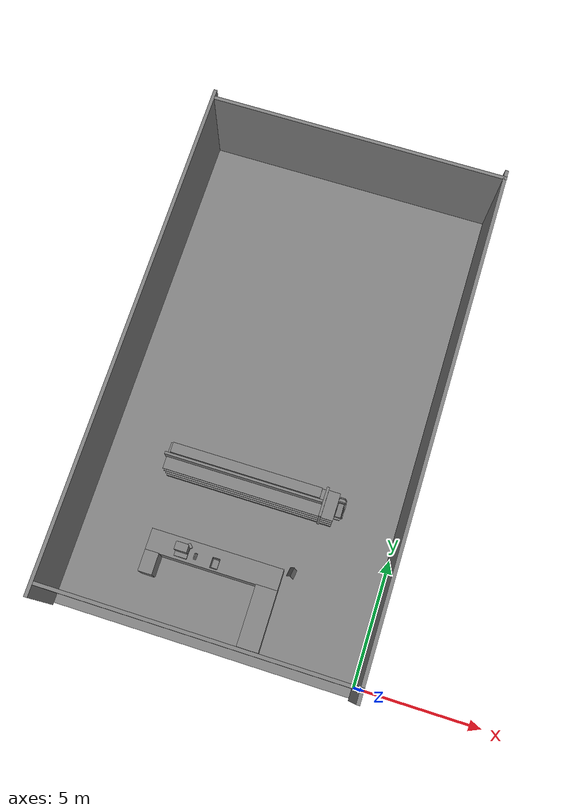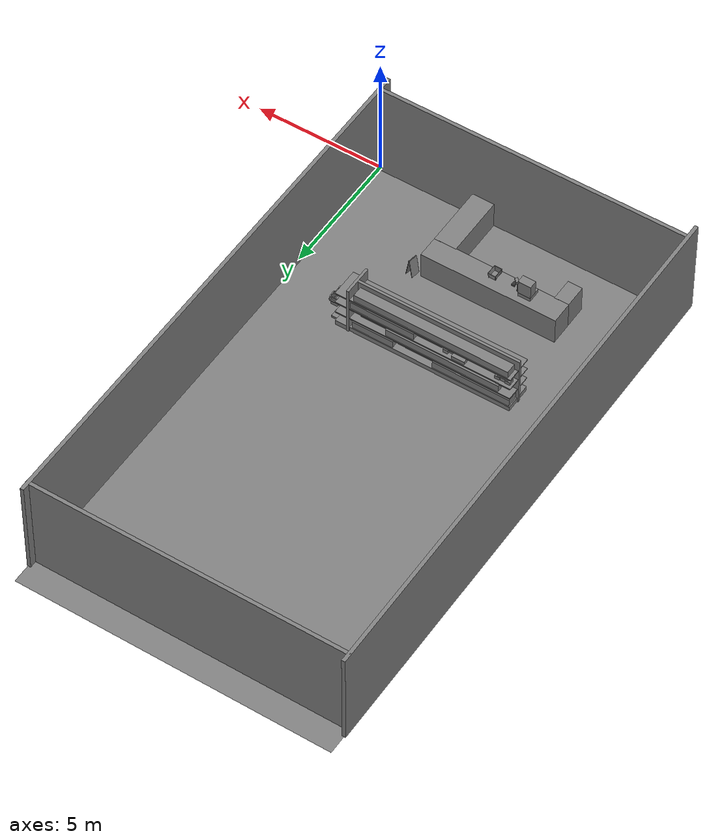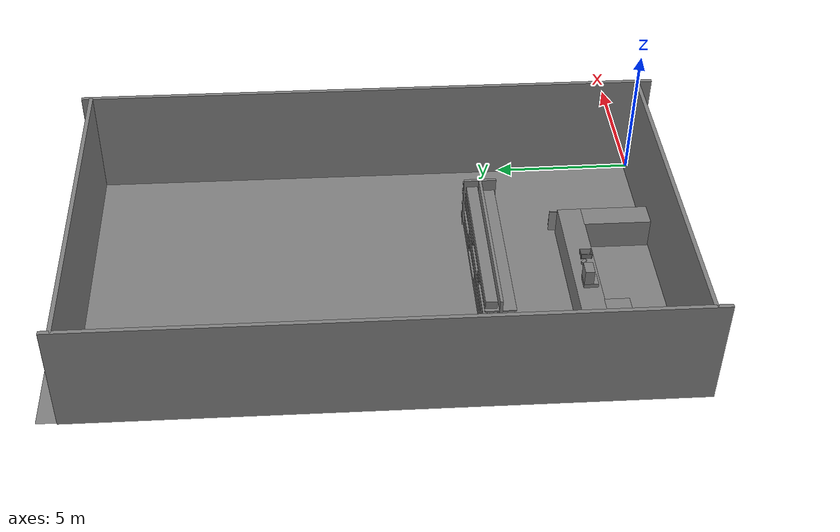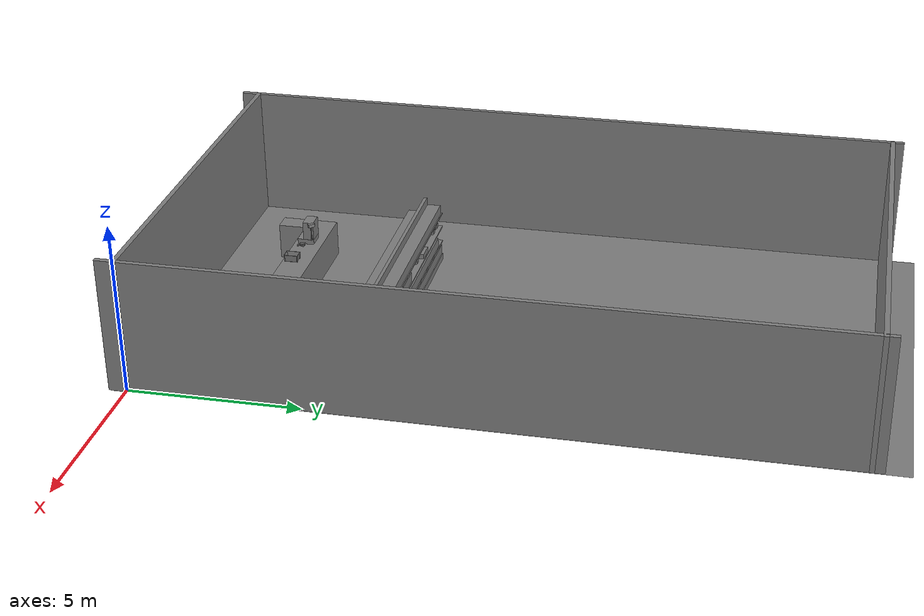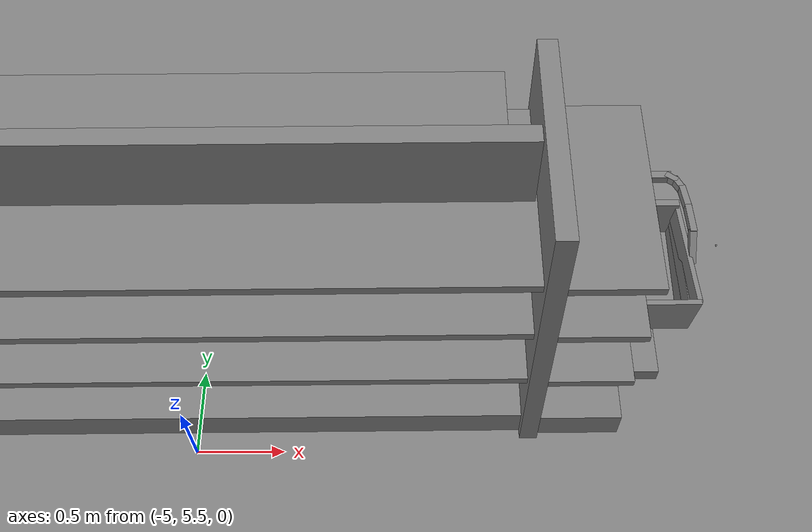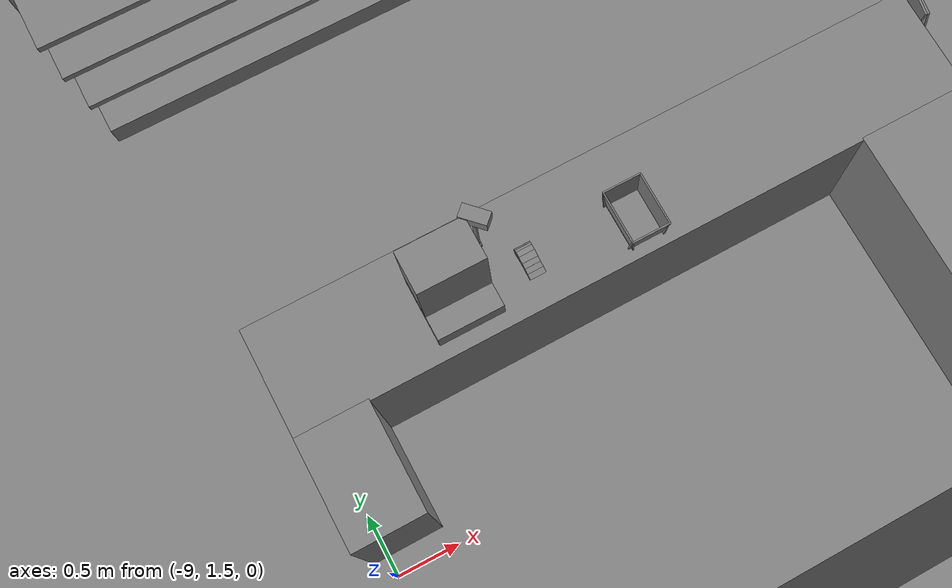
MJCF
<mujoco>
    <option gravity="0.000000000 0.000000000 -9.810000420" timestep="0.0166666" integrator="implicitfast" density="1.225" viscosity="1.8000001e-05" noslip_iterations="10" iterations="100" sdf_iterations="50">
        <flag multiccd="disable"/>
    </option>
    <size memory="1000M"/>
    <compiler coordinate="local"/>
    <worldbody>
        <light cutoff="30" pos="0 1 1" dir="0 -1 -2"/>
        <light cutoff="30" pos="0 -1 1" dir="0 1 -2"/>
        <body pos="-7.168000221 2.823999882 1.227496982" euler="-0.283413887 0.056829713 -0.133293241" name="openloong_gripper_2f85_fix_base_usda_Pos">
            <geom contype="1" conaffinity="1" density="1000" type="box" material="" rgba="0.500000000 0.500000000 0.500000000 1.000000000" solimp="0.899999976 0.949999988 0.001000000" friction="1.000000000 0.005000000 0.000100000" solref="0.020000000 1.000000000" margin="0" condim="3" group="0" pos="-0.002278805 0.074524641 -0.004134178" quat="0.315989256 0.948762834 0.000000000 0.000000000" size="0.059999999 0.013000000 0.035000000" name="openloong_gripper_2f85_fix_base_usda_geom_2CE47EBC_09A5_4330_A945_9922820932D0"/>
            <geom contype="1" conaffinity="1" density="1000" type="box" material="" rgba="0.500000000 0.500000000 0.500000000 1.000000000" solimp="0.899999976 0.949999988 0.001000000" friction="1.000000000 0.005000000 0.000100000" solref="0.020000000 1.000000000" margin="0" condim="3" group="0" pos="-0.002278805 0.078031301 0.008128285" quat="0.990447283 -0.137893349 -0.000000000 0.000000000" size="0.059999999 0.010000000 0.035000000" name="openloong_gripper_2f85_fix_base_usda_geom_9F57033F_CB90_42FB_B9A1_DF499E285945"/>
            <geom contype="1" conaffinity="1" density="1000" type="box" material="" rgba="0.500000000 0.500000000 0.500000000 1.000000000" solimp="0.899999976 0.949999988 0.001000000" friction="1.000000000 0.005000000 0.000100000" solref="0.020000000 1.000000000" margin="0" condim="3" group="0" pos="-0.002278805 0.080785275 -0.002596974" quat="0.287325412 -0.957833171 0.000000000 -0.000000000" size="0.059999999 0.013000000 0.035000000" name="openloong_gripper_2f85_fix_base_usda_geom_0323DDD2_F882_483B_9D99_375B52D5FC58"/>
            <geom contype="1" conaffinity="1" density="1000" type="box" material="" rgba="0.500000000 0.500000000 0.500000000 1.000000000" solimp="0.899999976 0.949999988 0.001000000" friction="1.000000000 0.005000000 0.000100000" solref="0.020000000 1.000000000" margin="0" condim="3" group="0" pos="-0.002278805 -0.098804474 -0.020147085" quat="0.988851428 0.148906425 0.000000000 -0.000000000" size="0.059999999 0.022000000 0.020000000" name="openloong_gripper_2f85_fix_base_usda_geom_0044E253_8816_4B07_89F3_84CD7A3F4965"/>
            <geom contype="1" conaffinity="1" density="1000" type="box" material="" rgba="0.500000000 0.500000000 0.500000000 1.000000000" solimp="0.899999976 0.949999988 0.001000000" friction="1.000000000 0.005000000 0.000100000" solref="0.020000000 1.000000000" margin="0" condim="3" group="0" pos="-0.002279282 0.019920349 0.012102842" quat="0.995421529 0.095583312 -0.000000000 0.000000000" size="0.059999999 0.025000000 0.026000001" name="openloong_gripper_2f85_fix_base_usda_geom_4B52481A_5A42_4248_8499_DF333940D966"/>
            <geom contype="1" conaffinity="1" density="1000" type="box" material="" rgba="0.500000000 0.500000000 0.500000000 1.000000000" solimp="0.899999976 0.949999988 0.001000000" friction="1.000000000 0.005000000 0.000100000" solref="0.020000000 1.000000000" margin="0" condim="3" group="0" pos="-0.002279282 0.005734444 -0.014276981" quat="0.999571502 -0.029275293 -0.000000000 0.000000000" size="0.059999999 0.050000001 0.010000000" name="openloong_gripper_2f85_fix_base_usda_geom_E9674ED1_E46D_4F5A_B910_4D74E50CDE1B"/>
            <geom contype="1" conaffinity="1" density="1000" type="box" material="" rgba="0.500000000 0.500000000 0.500000000 1.000000000" solimp="0.899999976 0.949999988 0.001000000" friction="1.000000000 0.005000000 0.000100000" solref="0.020000000 1.000000000" margin="0" condim="3" group="0" pos="-0.002278805 0.079460382 0.007771969" quat="0.922590315 -0.385781497 -0.000000000 0.000000000" size="0.059999999 0.010000000 0.035000000" name="openloong_gripper_2f85_fix_base_usda_geom_C093E078_AF2F_4BF9_8ED3_B6C9AD6D4077"/>
            <geom contype="1" conaffinity="1" density="1000" type="box" material="" rgba="0.500000000 0.500000000 0.500000000 1.000000000" solimp="0.899999976 0.949999988 0.001000000" friction="1.000000000 0.005000000 0.000100000" solref="0.020000000 1.000000000" margin="0" condim="3" group="0" pos="-0.002279282 0.081384182 -0.001320124" quat="0.590483606 -0.807049692 0.000000000 0.000000000" size="0.059999999 0.013000000 0.035000000" name="openloong_gripper_2f85_fix_base_usda_geom_6FE7BF31_B19F_445F_9A93_9B513D554452"/>
            <geom contype="1" conaffinity="1" density="1000" type="box" material="" rgba="0.500000000 0.500000000 0.500000000 1.000000000" solimp="0.899999976 0.949999988 0.001000000" friction="1.000000000 0.005000000 0.000100000" solref="0.020000000 1.000000000" margin="0" condim="3" group="0" pos="-0.002278805 -0.059297562 -0.007972836" quat="0.988851428 0.148906425 0.000000000 -0.000000000" size="0.059999999 0.020000000 0.022000000" name="openloong_gripper_2f85_fix_base_usda_geom_4CFAE43E_00A0_4714_9422_BC1A200562ED"/>
            <geom contype="1" conaffinity="1" density="1000" type="box" material="" rgba="0.500000000 0.500000000 0.500000000 1.000000000" solimp="0.899999976 0.949999988 0.001000000" friction="1.000000000 0.005000000 0.000100000" solref="0.020000000 1.000000000" margin="0" condim="3" group="0" pos="-0.002278805 0.076618671 -0.004656911" quat="0.004634960 0.999989390 -0.000000000 0.000000000" size="0.059999999 0.013000000 0.035000000" name="openloong_gripper_2f85_fix_base_usda_geom_1CF98C01_8476_4C37_B016_56FD74475806"/>
            <geom contype="1" conaffinity="1" density="1000" type="box" material="" rgba="0.500000000 0.500000000 0.500000000 1.000000000" solimp="0.899999976 0.949999988 0.001000000" friction="1.000000000 0.005000000 0.000100000" solref="0.020000000 1.000000000" margin="0" condim="3" group="0" pos="-0.002279282 -0.021952629 0.002959967" quat="0.991270185 0.131847635 0.000000000 -0.000000000" size="0.059999999 0.020000000 0.024000000" name="openloong_gripper_2f85_fix_base_usda_geom_A614AB93_B8C4_4CDA_A9A2_583B9DA3F035"/>
            <geom contype="1" conaffinity="1" density="1000" type="box" material="" rgba="0.500000000 0.500000000 0.500000000 1.000000000" solimp="0.899999976 0.949999988 0.001000000" friction="1.000000000 0.005000000 0.000100000" solref="0.020000000 1.000000000" margin="0" condim="3" group="0" pos="-0.002278805 0.081418991 0.002587795" quat="0.803492188 -0.595315576 0.000000000 0.000000000" size="0.059999999 0.013000000 0.035000000" name="openloong_gripper_2f85_fix_base_usda_geom_66827287_97CB_402C_8D50_F6CBB7EF055C"/>
            <geom contype="1" conaffinity="1" density="1000" type="box" material="" rgba="0.500000000 0.500000000 0.500000000 1.000000000" solimp="0.899999976 0.949999988 0.001000000" friction="1.000000000 0.005000000 0.000100000" solref="0.020000000 1.000000000" margin="0" condim="3" group="0" pos="-0.002278805 0.061115503 0.008545756" quat="0.999325931 0.036714435 -0.000000000 -0.000000000" size="0.059999999 0.020000000 0.035000000" name="openloong_gripper_2f85_fix_base_usda_geom_374133B8_24DE_4FC4_9926_416B63FC1C88"/>
            <freejoint name="openloong_gripper_2f85_fix_base_usda_pos_scan"/>
        </body>
        <body pos="-2.436573029 6.404376507 0.137849092" euler="0.000000000 0.000000000 0.000000000" name="openloong_gripper_2f85_fix_base_usda_shoppingtrolley_01">
            <geom contype="1" conaffinity="1" density="1000" type="box" material="" rgba="0.500000000 0.500000000 0.500000000 1.000000000" solimp="0.899999976 0.949999988 0.001000000" friction="1.000000000 0.005000000 0.000100000" solref="0.020000000 1.000000000" margin="0" condim="3" group="0" pos="-0.169898406 -0.178061336 0.864131629" quat="0.916343808 -0.400392294 -0.000000045 0.000000030" size="0.017999999 0.022499999 0.089999996" name="openloong_gripper_2f85_fix_base_usda_geom_E2D1FEFC_EBD2_4324_8BFC_68BA4DF13080"/>
            <geom contype="1" conaffinity="1" density="1000" type="box" material="" rgba="0.500000000 0.500000000 0.500000000 1.000000000" solimp="0.899999976 0.949999988 0.001000000" friction="1.000000000 0.005000000 0.000100000" solref="0.020000000 1.000000000" margin="0" condim="3" group="0" pos="-0.107458733 0.238907143 0.911498845" quat="0.634576976 0.622505128 -0.330067992 -0.317575932" size="0.017999999 0.022499999 0.035999998" name="openloong_gripper_2f85_fix_base_usda_geom_4EC0E3ED_050B_47F0_B1FD_14D2748735EF"/>
            <geom contype="1" conaffinity="1" density="1000" type="box" material="" rgba="0.500000000 0.500000000 0.500000000 1.000000000" solimp="0.899999976 0.949999988 0.001000000" friction="1.000000000 0.005000000 0.000100000" solref="0.020000000 1.000000000" margin="0" condim="3" group="0" pos="-0.005004787 0.248085022 0.912686050" quat="1.000000000 0.000000000 0.000000000 0.000000000" size="0.107999995 0.022499999 0.022499999" name="openloong_gripper_2f85_fix_base_usda_geom_7F020217_9572_4536_9CB2_1E6293F68CBC"/>
            <geom contype="1" conaffinity="1" density="1000" type="box" material="" rgba="0.500000000 0.500000000 0.500000000 1.000000000" solimp="0.899999976 0.949999988 0.001000000" friction="1.000000000 0.005000000 0.000100000" solref="0.020000000 1.000000000" margin="0" condim="3" group="0" pos="0.131482959 -0.182533979 0.598989725" quat="0.996607125 0.055331629 0.059003670 0.015205893" size="0.013499999 0.287999988 0.053999998" name="openloong_gripper_2f85_fix_base_usda_geom_DE24CE59_AC5C_4B8D_959F_E1851BDC5113"/>
            <geom contype="1" conaffinity="1" density="1000" type="box" material="" rgba="0.500000000 0.500000000 0.500000000 1.000000000" solimp="0.899999976 0.949999988 0.001000000" friction="1.000000000 0.005000000 0.000100000" solref="0.020000000 1.000000000" margin="0" condim="3" group="0" pos="-0.000005364 0.100332208 0.734785020" quat="0.999668717 0.025737956 -0.000000010 0.000000000" size="0.135000005 0.019800000 0.152999997" name="openloong_gripper_2f85_fix_base_usda_geom_4154BB51_DE98_403C_B2BC_13AEB935A22F"/>
            <geom contype="1" conaffinity="1" density="1000" type="box" material="" rgba="0.500000000 0.500000000 0.500000000 1.000000000" solimp="0.899999976 0.949999988 0.001000000" friction="1.000000000 0.005000000 0.000100000" solref="0.020000000 1.000000000" margin="0" condim="3" group="0" pos="-0.126757339 -0.182533979 0.598989725" quat="0.996607184 0.055331606 -0.059003651 -0.015205891" size="0.013499999 0.287999988 0.053999998" name="openloong_gripper_2f85_fix_base_usda_geom_854A8E6D_5E58_4513_8D1A_FBA56D3D9700"/>
            <geom contype="1" conaffinity="1" density="1000" type="box" material="" rgba="0.500000000 0.500000000 0.500000000 1.000000000" solimp="0.899999976 0.949999988 0.001000000" friction="1.000000000 0.005000000 0.000100000" solref="0.020000000 1.000000000" margin="0" condim="3" group="0" pos="-0.134013891 0.200098798 0.912192523" quat="0.694057047 0.679413557 -0.172947660 -0.163618833" size="0.017999999 0.022499999 0.035999998" name="openloong_gripper_2f85_fix_base_usda_geom_D433E67B_4C05_4DEF_94BE_EC61D2732DC7"/>
            <geom contype="1" conaffinity="1" density="1000" type="box" material="" rgba="0.500000000 0.500000000 0.500000000 1.000000000" solimp="0.899999976 0.949999988 0.001000000" friction="1.000000000 0.005000000 0.000100000" solref="0.020000000 1.000000000" margin="0" condim="3" group="0" pos="0.141839072 -0.191051379 0.702451229" quat="0.997147262 0.056065105 0.045779929 0.021407485" size="0.013499999 0.287999988 0.053999998" name="openloong_gripper_2f85_fix_base_usda_geom_479B0647_BACA_4AA2_8CEC_0CFEE46CA38E"/>
            <geom contype="1" conaffinity="1" density="1000" type="box" material="" rgba="0.500000000 0.500000000 0.500000000 1.000000000" solimp="0.899999976 0.949999988 0.001000000" friction="1.000000000 0.005000000 0.000100000" solref="0.020000000 1.000000000" margin="0" condim="3" group="0" pos="-0.135714188 -0.191051379 0.694841146" quat="0.997147322 0.056064609 -0.045779683 -0.021407485" size="0.013499999 0.287999988 0.053999998" name="openloong_gripper_2f85_fix_base_usda_geom_47F70249_88F2_4762_A672_84F9D75A9A42"/>
            <geom contype="1" conaffinity="1" density="1000" type="box" material="" rgba="0.500000000 0.500000000 0.500000000 1.000000000" solimp="0.899999976 0.949999988 0.001000000" friction="1.000000000 0.005000000 0.000100000" solref="0.020000000 1.000000000" margin="0" condim="3" group="0" pos="-0.000004721 -0.174527690 0.560063601" quat="0.996704638 0.081116498 -0.000000004 0.000000000" size="0.126000002 0.287999988 0.009000000" name="openloong_gripper_2f85_fix_base_usda_geom_B773E12C_44D8_42C7_A4DC_4E98C25DAD49"/>
            <geom contype="1" conaffinity="1" density="1000" type="box" material="" rgba="0.500000000 0.500000000 0.500000000 1.000000000" solimp="0.899999976 0.949999988 0.001000000" friction="1.000000000 0.005000000 0.000100000" solref="0.020000000 1.000000000" margin="0" condim="3" group="0" pos="0.134013891 0.200098798 0.912192523" quat="0.692574680 -0.680924535 -0.166899428 0.169783980" size="0.017999999 0.022499999 0.035999998" name="openloong_gripper_2f85_fix_base_usda_geom_5F81A707_53E4_4927_A9FA_B8D9E696E0F0"/>
            <geom contype="1" conaffinity="1" density="1000" type="box" material="" rgba="0.500000000 0.500000000 0.500000000 1.000000000" solimp="0.899999976 0.949999988 0.001000000" friction="1.000000000 0.005000000 0.000100000" solref="0.020000000 1.000000000" margin="0" condim="3" group="0" pos="-0.012634277 -0.174527690 -0.088243507" quat="1.000000000 0.000000000 -0.000000004 0.000000000" size="0.135000005 0.287999988 0.044999998" name="openloong_gripper_2f85_fix_base_usda_geom_627E06F7_D414_4141_8979_210C0174579C"/>
            <geom contype="1" conaffinity="1" density="1000" type="box" material="" rgba="0.500000000 0.500000000 0.500000000 1.000000000" solimp="0.899999976 0.949999988 0.001000000" friction="1.000000000 0.005000000 0.000100000" solref="0.020000000 1.000000000" margin="0" condim="3" group="0" pos="-0.142927840 -0.199506134 0.784674108" quat="0.998421252 0.016904408 -0.027109101 -0.046199299" size="0.013499999 0.305999994 0.063000001" name="openloong_gripper_2f85_fix_base_usda_geom_8EEE6286_1B03_4CDF_A2E0_E266609353A2"/>
            <geom contype="1" conaffinity="1" density="1000" type="box" material="" rgba="0.500000000 0.500000000 0.500000000 1.000000000" solimp="0.899999976 0.949999988 0.001000000" friction="1.000000000 0.005000000 0.000100000" solref="0.020000000 1.000000000" margin="0" condim="3" group="0" pos="-0.169898406 -0.043119621 0.915120542" quat="0.687021017 0.726584017 -0.005590606 -0.006832919" size="0.017999999 0.022499999 0.089999996" name="openloong_gripper_2f85_fix_base_usda_geom_64AFE6F4_4F8A_4556_8D60_5157DD85A621"/>
            <geom contype="1" conaffinity="1" density="1000" type="box" material="" rgba="0.500000000 0.500000000 0.500000000 1.000000000" solimp="0.899999976 0.949999988 0.001000000" friction="1.000000000 0.005000000 0.000100000" solref="0.020000000 1.000000000" margin="0" condim="3" group="0" pos="-0.000006008 -0.484932661 0.670727849" quat="0.997585475 0.069449045 -0.000000004 -0.000000089" size="0.179999992 0.013499999 0.170999989" name="openloong_gripper_2f85_fix_base_usda_geom_57FF62AA_BED8_4681_85E1_E80A372EFE70"/>
            <geom contype="1" conaffinity="1" density="1000" type="box" material="" rgba="0.500000000 0.500000000 0.500000000 1.000000000" solimp="0.899999976 0.949999988 0.001000000" friction="1.000000000 0.005000000 0.000100000" solref="0.020000000 1.000000000" margin="0" condim="3" group="0" pos="0.160832971 0.103427693 0.910528183" quat="0.711112797 -0.700149298 -0.042821646 0.047705106" size="0.017999999 0.022499999 0.071999997" name="openloong_gripper_2f85_fix_base_usda_geom_578B1DA4_7973_4A70_A014_482F9A6D1FAE"/>
            <geom contype="1" conaffinity="1" density="1000" type="box" material="" rgba="0.500000000 0.500000000 0.500000000 1.000000000" solimp="0.899999976 0.949999988 0.001000000" friction="1.000000000 0.005000000 0.000100000" solref="0.020000000 1.000000000" margin="0" condim="3" group="0" pos="-0.160832763 0.103427693 0.910528183" quat="0.711469591 0.699786782 -0.048386075 -0.042050660" size="0.017999999 0.022499999 0.071999997" name="openloong_gripper_2f85_fix_base_usda_geom_CEBF90D4_B4E3_42BC_9326_BEDDC5E24430"/>
            <geom contype="1" conaffinity="1" density="1000" type="box" material="" rgba="0.500000000 0.500000000 0.500000000 1.000000000" solimp="0.899999976 0.949999988 0.001000000" friction="1.000000000 0.005000000 0.000100000" solref="0.020000000 1.000000000" margin="0" condim="3" group="0" pos="0.169898629 -0.178061336 0.864131629" quat="0.916343808 -0.400392294 -0.000000045 0.000000030" size="0.017999999 0.022499999 0.089999996" name="openloong_gripper_2f85_fix_base_usda_geom_4D3BF200_55D0_43C7_A040_8EB486F4B96B"/>
            <geom contype="1" conaffinity="1" density="1000" type="box" material="" rgba="0.500000000 0.500000000 0.500000000 1.000000000" solimp="0.899999976 0.949999988 0.001000000" friction="1.000000000 0.005000000 0.000100000" solref="0.020000000 1.000000000" margin="0" condim="3" group="0" pos="0.103667587 0.233050480 0.912927270" quat="0.634205043 -0.622199059 -0.324503720 0.324576139" size="0.017999999 0.022499999 0.035999998" name="openloong_gripper_2f85_fix_base_usda_geom_A423D6C4_FC24_4C52_836D_8B2951CE8E90"/>
            <geom contype="1" conaffinity="1" density="1000" type="box" material="" rgba="0.500000000 0.500000000 0.500000000 1.000000000" solimp="0.899999976 0.949999988 0.001000000" friction="1.000000000 0.005000000 0.000100000" solref="0.020000000 1.000000000" margin="0" condim="3" group="0" pos="0.169898629 -0.043119621 0.915120542" quat="0.687029123 -0.726576388 -0.006509603 0.005963952" size="0.017999999 0.022499999 0.089999996" name="openloong_gripper_2f85_fix_base_usda_geom_B5F12354_6C7A_4F74_A984_BA0590AAAC4D"/>
            <geom contype="1" conaffinity="1" density="1000" type="box" material="" rgba="0.500000000 0.500000000 0.500000000 1.000000000" solimp="0.899999976 0.949999988 0.001000000" friction="1.000000000 0.005000000 0.000100000" solref="0.020000000 1.000000000" margin="0" condim="3" group="0" pos="0.148195267 -0.199506566 0.782808602" quat="0.998808920 0.017156634 0.026950166 0.036880098" size="0.013499999 0.305999994 0.063000001" name="openloong_gripper_2f85_fix_base_usda_geom_9FA29A27_4843_4C25_A3EB_E2E2F128F1ED"/>
            <freejoint name="openloong_gripper_2f85_fix_base_usda_shoppingtrolley_01_joint"/>
            <site size="0.005000000 0.005000000 0.005000000" rgba="0.500000000 0.500000000 0.500000000 1.000000000" pos="0.000000000 0.000000000 0.000000000" quat="1.000000000 0.000000000 0.000000000 0.000000000" group="0" type="sphere" name="openloong_gripper_2f85_fix_base_usda_shoppingtrolley_01"/>
        </body>
        <body pos="-6.332345009 2.779978037 1.034067392" euler="0.000000000 0.000000000 0.000000000" name="openloong_gripper_2f85_fix_base_usda_basket">
            <geom contype="1" conaffinity="1" density="100000" type="box" material="" rgba="0.500000000 0.500000000 0.500000000 1.000000000" solimp="0.899999976 0.949999988 0.001000000" friction="1.000000000 0.899999976 0.000100000" solref="0.020000000 1.000000000" margin="0" condim="3" group="0" pos="-0.172339439 0.000000000 0.168361664" quat="0.706172407 -0.036353018 -0.036353093 0.706170976" size="0.200000003 0.006000000 0.108000003" name="openloong_gripper_2f85_fix_base_usda_geom_2752F6D9_5EC7_42B1_AC5E_3645E143271B"/>
            <geom contype="1" conaffinity="1" density="100000" type="box" material="" rgba="0.500000000 0.500000000 0.500000000 1.000000000" solimp="0.899999976 0.949999988 0.001000000" friction="1.000000000 0.899999976 0.000100000" solref="0.020000000 1.000000000" margin="0" condim="3" group="0" pos="-0.039724827 -0.188568115 0.167089701" quat="0.997537494 0.070135131 0.000000000 0.000000000" size="0.150000006 0.006000000 0.108000003" name="openloong_gripper_2f85_fix_base_usda_geom_17A6EFEF_A10B_411E_AFB5_DC9C68F106E9"/>
            <geom contype="1" conaffinity="1" density="100000" type="box" material="" rgba="0.500000000 0.500000000 0.500000000 1.000000000" solimp="0.899999976 0.949999988 0.001000000" friction="1.000000000 0.899999976 0.000100000" solref="0.020000000 1.000000000" margin="0" condim="3" group="0" pos="-0.039724827 0.188377380 0.167089701" quat="0.997489929 -0.070808925 0.000000000 0.000000000" size="0.150000006 0.006000000 0.108000003" name="openloong_gripper_2f85_fix_base_usda_geom_73398327_80F3_43C4_B96D_F5C82DE89598"/>
            <geom contype="1" conaffinity="1" density="100000" type="box" material="" rgba="0.500000000 0.500000000 0.500000000 1.000000000" solimp="0.899999976 0.949999988 0.001000000" friction="1.000000000 0.899999976 0.000100000" solref="0.020000000 1.000000000" margin="0" condim="3" group="0" pos="-0.039724827 0.000000000 0.068126202" quat="1.000000000 0.000000000 0.000000000 0.000000000" size="0.129999995 0.174999997 0.006000000" name="openloong_gripper_2f85_fix_base_usda_geom_DE547577_0A30_4393_994C_A1FC0DF3A78A"/>
            <geom contype="1" conaffinity="1" density="100000" type="box" material="" rgba="0.500000000 0.500000000 0.500000000 1.000000000" solimp="0.899999976 0.949999988 0.001000000" friction="1.000000000 0.899999976 0.000100000" solref="0.020000000 1.000000000" margin="0" condim="3" group="0" pos="0.094372749 0.000000000 0.168361664" quat="0.706172049 0.036353335 0.036353379 0.706171215" size="0.200000003 0.006000000 0.108000003" name="openloong_gripper_2f85_fix_base_usda_geom_A0AA0BB2_0AF3_4FDB_84E5_7F621DEE5C40"/>
            <freejoint name="openloong_gripper_2f85_fix_base_usda_basket_joint"/>
            <site size="0.005000000 0.005000000 0.005000000" rgba="0.500000000 0.500000000 0.500000000 1.000000000" pos="0.000000000 0.000000000 0.000000000" quat="1.000000000 0.000000000 0.000000000 0.000000000" group="0" type="sphere" name="openloong_gripper_2f85_fix_base_usda_basketsite"/>
        </body>
        <body pos="-3.510578632 3.403555870 -0.000000100" euler="0.000000000 0.000000000 40.200675964" name="openloong_gripper_2f85_fix_base_usda_PZ">
            <geom contype="1" conaffinity="1" density="1000" type="box" material="" rgba="0.500000000 0.500000000 0.500000000 1.000000000" solimp="0.899999976 0.949999988 0.001000000" friction="1.000000000 0.005000000 0.000100000" solref="0.020000000 1.000000000" margin="0" condim="3" group="0" pos="-0.047453165 0.056484699 0.373715430" quat="0.934750080 0.077914521 0.028795123 0.345459938" size="0.180000007 0.010000000 0.379999995" name="openloong_gripper_2f85_fix_base_usda_geom_EE664BE3_262F_48A3_A572_9245D4226922"/>
            <geom contype="1" conaffinity="1" density="1000" type="box" material="" rgba="0.500000000 0.500000000 0.500000000 1.000000000" solimp="0.899999976 0.949999988 0.001000000" friction="1.000000000 0.005000000 0.000100000" solref="0.020000000 1.000000000" margin="0" condim="3" group="0" pos="0.047452450 -0.054376602 0.374072611" quat="0.934387863 -0.082143910 -0.030358355 0.345326364" size="0.180000007 0.010000000 0.379999995" name="openloong_gripper_2f85_fix_base_usda_geom_CB2873BD_844E_41ED_92A1_46836F2BE2A3"/>
            <freejoint name="openloong_gripper_2f85_fix_base_usda_PZ"/>
        </body>
        <body pos="0.000000000 0.000000000 0.000000000" euler="0.000000000 0.000000000 0.000000000" name="Interactive Objects_Interactive Objects"/>
        <body pos="0.000000000 0.000000000 0.000000000" euler="0.000000000 0.000000000 0.000000000" name=" Static Objects_ Static Objects">
            <geom contype="1" conaffinity="1" density="1000" type="box" material="" rgba="0.500000000 0.500000000 0.500000000 1.000000000" solimp="0.899999976 0.949999988 0.001000000" friction="1.000000000 0.005000000 0.000100000" solref="0.020000000 1.000000000" margin="0" condim="3" group="0" pos="-3.101639986 6.150595188 1.018643856" quat="1.000000000 0.000000000 0.000000000 0.000000000" size="0.050000001 0.579999983 1.019999981" name=" Static Objects_geom_6A81BB0C_1185_4D92_807B_DC81B1658010"/>
            <geom contype="1" conaffinity="1" density="1000" type="box" material="" rgba="0.500000000 0.500000000 0.500000000 1.000000000" solimp="0.899999976 0.949999988 0.001000000" friction="1.000000000 0.005000000 0.000100000" solref="0.020000000 1.000000000" margin="0" condim="3" group="0" pos="-2.825197220 6.153595448 1.115278244" quat="0.707107067 0.000000000 0.000000000 0.707106471" size="0.550000012 0.239999995 0.025000000" name=" Static Objects_geom_1269DC84_3B56_455B_99D2_A04895578697"/>
            <geom contype="1" conaffinity="1" density="1000" type="box" material="" rgba="0.500000000 0.500000000 0.500000000 1.000000000" solimp="0.899999976 0.949999988 0.001000000" friction="1.000000000 0.005000000 0.000100000" solref="0.020000000 1.000000000" margin="0" condim="3" group="0" pos="-2.825197220 6.153595448 0.097434282" quat="0.707107067 0.000000000 0.000000000 0.707106471" size="0.550000012 0.239999995 0.098999999" name=" Static Objects_geom_40313EAD_C892_48FA_8E43_204C6A9A664D"/>
            <geom contype="1" conaffinity="1" density="1000" type="box" material="" rgba="0.500000000 0.500000000 0.500000000 1.000000000" solimp="0.899999976 0.949999988 0.001000000" friction="1.000000000 0.005000000 0.000100000" solref="0.020000000 1.000000000" margin="0" condim="3" group="0" pos="-6.293097973 6.153595448 1.114443064" quat="0.707107067 0.000000000 0.000000000 0.707106471" size="0.529999971 3.134999990 0.025000000" name=" Static Objects_geom_5D9522CA_B368_4570_AE04_2AABA3597150"/>
            <geom contype="1" conaffinity="1" density="1000" type="box" material="" rgba="0.500000000 0.500000000 0.500000000 1.000000000" solimp="0.899999976 0.949999988 0.001000000" friction="1.000000000 0.005000000 0.000100000" solref="0.020000000 1.000000000" margin="0" condim="3" group="0" pos="-6.286010742 6.153595448 0.096129179" quat="0.707107067 0.000000000 0.000000000 0.707106471" size="0.529999971 3.134999990 0.098999999" name=" Static Objects_geom_DFFD3735_E571_47D7_897F_F10DF2A5119A"/>
            <geom contype="1" conaffinity="1" density="1000" type="box" material="" rgba="0.500000000 0.500000000 0.500000000 1.000000000" solimp="0.899999976 0.949999988 0.001000000" friction="1.000000000 0.005000000 0.000100000" solref="0.020000000 1.000000000" margin="0" condim="3" group="0" pos="-2.825197220 6.153595448 1.563861728" quat="0.707107067 0.000000000 0.000000000 0.707106471" size="0.550000012 0.239999995 0.025000000" name=" Static Objects_geom_D8CA7E73_D516_474B_B2EB_9CC41AD4C885"/>
            <geom contype="1" conaffinity="1" density="1000" type="box" material="" rgba="0.500000000 0.500000000 0.500000000 1.000000000" solimp="0.899999976 0.949999988 0.001000000" friction="1.000000000 0.005000000 0.000100000" solref="0.020000000 1.000000000" margin="0" condim="3" group="0" pos="-6.311686516 6.153595448 1.018643856" quat="0.707107067 0.000000000 0.000000000 0.707106471" size="0.050000001 3.150000095 1.019999981" name=" Static Objects_geom_3254F35C_FB49_4130_B0F3_5BE2E188BD51"/>
            <geom contype="1" conaffinity="1" density="1000" type="box" material="" rgba="0.500000000 0.500000000 0.500000000 1.000000000" solimp="0.899999976 0.949999988 0.001000000" friction="1.000000000 0.005000000 0.000100000" solref="0.020000000 1.000000000" margin="0" condim="3" group="0" pos="-2.825197220 6.153595448 0.629031777" quat="0.707107067 0.000000000 0.000000000 0.707106471" size="0.550000012 0.239999995 0.025000000" name=" Static Objects_geom_7A0E42E5_0F28_478D_87F5_203DABE9BAE4"/>
            <geom contype="1" conaffinity="1" density="1000" type="box" material="" rgba="0.500000000 0.500000000 0.500000000 1.000000000" solimp="0.899999976 0.949999988 0.001000000" friction="1.000000000 0.005000000 0.000100000" solref="0.020000000 1.000000000" margin="0" condim="3" group="0" pos="-6.286010742 6.153595448 1.563861728" quat="0.707107067 0.000000000 0.000000000 0.707106471" size="0.529999971 3.134999990 0.025000000" name=" Static Objects_geom_975B4ED7_7977_4CBE_9635_774EC38B16EF"/>
            <geom contype="1" conaffinity="1" density="1000" type="box" material="" rgba="0.500000000 0.500000000 0.500000000 1.000000000" solimp="0.899999976 0.949999988 0.001000000" friction="1.000000000 0.005000000 0.000100000" solref="0.020000000 1.000000000" margin="0" condim="3" group="0" pos="-6.286010742 6.153595448 0.629031777" quat="0.707107067 0.000000000 0.000000000 0.707106471" size="0.529999971 3.134999990 0.025000000" name=" Static Objects_geom_6573AD5E_42B0_4E31_8227_C766AEF80926"/>
            <geom contype="1" conaffinity="1" density="1000" type="box" material="" rgba="0.500000000 0.500000000 0.500000000 1.000000000" solimp="0.899999976 0.949999988 0.001000000" friction="1.000000000 0.005000000 0.000100000" solref="0.020000000 1.000000000" margin="0" condim="3" group="0" pos="-7.719123363 2.867671013 1.173410416" quat="1.000000000 0.000000000 0.000000000 0.000000000" size="0.250000000 0.250000000 0.079999998" name=" Static Objects_geom_A5078194_4433_49B3_BDF9_ECA88BA2BBCE"/>
            <geom contype="1" conaffinity="1" density="1000" type="box" material="" rgba="0.500000000 0.500000000 0.500000000 1.000000000" solimp="0.899999976 0.949999988 0.001000000" friction="1.000000000 0.005000000 0.000100000" solref="0.020000000 1.000000000" margin="0" condim="3" group="0" pos="-7.408766270 3.088089943 1.776644945" quat="0.928051054 0.000000000 0.000000000 0.372453064" size="0.050000001 0.100000001 0.050000001" name=" Static Objects_geom_81B1B597_2014_431A_A566_CCA1BCE1ECDD"/>
            <geom contype="1" conaffinity="1" density="1000" type="box" material="" rgba="0.500000000 0.500000000 0.500000000 1.000000000" solimp="0.899999976 0.949999988 0.001000000" friction="1.000000000 0.005000000 0.000100000" solref="0.020000000 1.000000000" margin="0" condim="3" group="0" pos="-7.719123363 2.958004713 1.530241251" quat="1.000000000 0.000000000 0.000000000 0.000000000" size="0.250000000 0.159999996 0.280000001" name=" Static Objects_geom_E6BAF3A1_582C_4F39_BDD3_B6EEF865BF4F"/>
            <geom contype="1" conaffinity="1" density="1000" type="cylinder" material="" rgba="0.500000000 0.500000000 0.500000000 1.000000000" solimp="0.899999976 0.949999988 0.001000000" friction="1.000000000 0.005000000 0.000100000" solref="0.020000000 1.000000000" margin="0" condim="3" group="0" pos="-7.427312374 3.069516420 1.502544641" quat="0.928051054 0.000000000 0.000000000 0.372453064" size="0.015000000 0.230000004 0.100000001" name=" Static Objects_geom_E01AA21D_D01A_4241_BADD_F71F9919B2C8"/>
            <geom contype="1" conaffinity="1" density="1000" type="box" material="" rgba="0.500000000 0.500000000 0.500000000 1.000000000" solimp="0.899999976 0.949999988 0.001000000" friction="1.000000000 0.005000000 0.000100000" solref="0.020000000 1.000000000" margin="0" condim="3" group="0" pos="-7.437745571 3.067511320 1.289965630" quat="1.000000000 0.000000000 0.000000000 0.000000000" size="0.029999999 0.020000000 0.020000000" name=" Static Objects_geom_9A33C756_1EB2_4EAC_8E98_5E55036567F3"/>
            <geom contype="1" conaffinity="1" density="1000" type="box" material="" rgba="0.500000000 0.500000000 0.500000000 1.000000000" solimp="0.899999976 0.949999988 0.001000000" friction="1.000000000 0.005000000 0.000100000" solref="0.020000000 1.000000000" margin="0" condim="3" group="0" pos="-9.058088303 6.434794426 1.209077358" quat="1.000000000 0.000000000 0.000000000 0.000000000" size="0.250000000 0.100000001 0.070000000" name=" Static Objects_geom_8C6CE683_D4E5_4CA2_B9ED_6FA0C1608D6B"/>
            <geom contype="1" conaffinity="1" density="1000" type="box" material="" rgba="0.500000000 0.500000000 0.500000000 1.000000000" solimp="0.899999976 0.949999988 0.001000000" friction="1.000000000 0.005000000 0.000100000" solref="0.020000000 1.000000000" margin="0" condim="3" group="0" pos="-7.886891365 6.459744930 0.352518857" quat="1.000000000 0.000000000 0.000000000 0.000000000" size="1.500000000 0.200000003 0.150000006" name=" Static Objects_geom_2FFD12E6_2A2D_4936_9C7C_2F198A8B8CA6"/>
            <geom contype="1" conaffinity="1" density="1000" type="box" material="" rgba="0.500000000 0.500000000 0.500000000 1.000000000" solimp="0.899999976 0.949999988 0.001000000" friction="1.000000000 0.005000000 0.000100000" solref="0.020000000 1.000000000" margin="0" condim="3" group="0" pos="-9.237723351 6.464855671 1.209077358" quat="1.000000000 0.000000000 0.000000000 0.000000000" size="0.100000001 0.100000001 0.070000000" name=" Static Objects_geom_99704BDF_ACA5_45CB_925F_97BCA0D9659B"/>
            <geom contype="1" conaffinity="1" density="1000" type="box" material="" rgba="0.500000000 0.500000000 0.500000000 1.000000000" solimp="0.899999976 0.949999988 0.001000000" friction="1.000000000 0.005000000 0.000100000" solref="0.020000000 1.000000000" margin="0" condim="3" group="0" pos="-6.924745083 6.362090111 1.214329123" quat="1.000000000 0.000000000 0.000000000 0.000000000" size="0.200000003 0.100000001 0.075000003" name=" Static Objects_geom_927E5D19_AF9E_4987_A8AC_27AB6F7B7BEB"/>
            <geom contype="1" conaffinity="1" density="1000" type="box" material="" rgba="0.500000000 0.500000000 0.500000000 1.000000000" solimp="0.899999976 0.949999988 0.001000000" friction="1.000000000 0.005000000 0.000100000" solref="0.020000000 1.000000000" margin="0" condim="3" group="0" pos="-4.407354832 6.459744930 1.292199373" quat="1.000000000 0.000000000 0.000000000 0.000000000" size="1.240000010 0.200000003 0.150000006" name=" Static Objects_geom_7CBF04F3_E5BB_4BA2_B63C_5E405D38579C"/>
            <geom contype="1" conaffinity="1" density="1000" type="box" material="" rgba="0.500000000 0.500000000 0.500000000 1.000000000" solimp="0.899999976 0.949999988 0.001000000" friction="1.000000000 0.005000000 0.000100000" solref="0.020000000 1.000000000" margin="0" condim="3" group="0" pos="-5.611940861 6.318420410 0.350975692" quat="1.000000000 0.000000000 0.000000000 0.000000000" size="0.699999988 0.100000001 0.150000006" name=" Static Objects_geom_95F9E767_130F_4BB5_A3DA_82339E50D016"/>
            <geom contype="1" conaffinity="1" density="1000" type="box" material="" rgba="0.500000000 0.500000000 0.500000000 1.000000000" solimp="0.899999976 0.949999988 0.001000000" friction="1.000000000 0.005000000 0.000100000" solref="0.020000000 1.000000000" margin="0" condim="3" group="0" pos="-6.300771236 6.459744930 1.744376063" quat="1.000000000 0.000000000 0.000000000 0.000000000" size="3.000000000 0.200000003 0.150000006" name=" Static Objects_geom_328169B4_AF0C_4927_BEF8_BA34FD222D65"/>
            <geom contype="1" conaffinity="1" density="1000" type="box" material="" rgba="0.500000000 0.500000000 0.500000000 1.000000000" solimp="0.899999976 0.949999988 0.001000000" friction="1.000000000 0.005000000 0.000100000" solref="0.020000000 1.000000000" margin="0" condim="3" group="0" pos="-6.751636982 6.459744930 0.800981164" quat="1.000000000 0.000000000 0.000000000 0.000000000" size="2.200000048 0.200000003 0.150000006" name=" Static Objects_geom_D9019471_F7B5_4D93_B69F_32B3AFD269A6"/>
            <geom contype="1" conaffinity="1" density="1000" type="box" material="" rgba="0.500000000 0.500000000 0.500000000 1.000000000" solimp="0.899999976 0.949999988 0.001000000" friction="1.000000000 0.005000000 0.000100000" solref="0.020000000 1.000000000" margin="0" condim="3" group="0" pos="-8.844120979 6.464855671 1.209077358" quat="1.000000000 0.000000000 0.000000000 0.000000000" size="0.100000001 0.100000001 0.070000000" name=" Static Objects_geom_0D9A9501_DE47_4342_8BBB_B0148920373A"/>
            <geom contype="1" conaffinity="1" density="1000" type="box" material="" rgba="0.500000000 0.500000000 0.500000000 1.000000000" solimp="0.899999976 0.949999988 0.001000000" friction="1.000000000 0.005000000 0.000100000" solref="0.020000000 1.000000000" margin="0" condim="3" group="0" pos="-6.098561764 6.327973843 1.292199373" quat="1.000000000 0.000000000 0.000000000 0.000000000" size="0.500000000 0.100000001 0.150000006" name=" Static Objects_geom_681B4009_3495_4114_9B81_03C5247464FB"/>
            <geom contype="1" conaffinity="1" density="1000" type="box" material="" rgba="0.500000000 0.500000000 0.500000000 1.000000000" solimp="0.899999976 0.949999988 0.001000000" friction="1.000000000 0.005000000 0.000100000" solref="0.020000000 1.000000000" margin="0" condim="3" group="0" pos="-6.824534416 6.447464466 1.212718010" quat="1.000000000 0.000000000 0.000000000 0.000000000" size="0.100000001 0.100000001 0.075000003" name=" Static Objects_geom_FC2163A0_F5AA_4D72_8402_9AF607A9B147"/>
            <geom contype="1" conaffinity="1" density="1000" type="box" material="" rgba="0.500000000 0.500000000 0.500000000 1.000000000" solimp="0.899999976 0.949999988 0.001000000" friction="1.000000000 0.005000000 0.000100000" solref="0.020000000 1.000000000" margin="0" condim="3" group="0" pos="-3.907610416 6.318625927 0.800981164" quat="1.000000000 0.000000000 0.000000000 0.000000000" size="0.500000000 0.100000001 0.150000006" name=" Static Objects_geom_6D41D1AF_E4A0_4EE2_9A75_E2A6D662DA3A"/>
            <geom contype="1" conaffinity="1" density="1000" type="box" material="" rgba="0.500000000 0.500000000 0.500000000 1.000000000" solimp="0.899999976 0.949999988 0.001000000" friction="1.000000000 0.005000000 0.000100000" solref="0.020000000 1.000000000" margin="0" condim="3" group="0" pos="-7.373087406 6.458900928 1.214329123" quat="1.000000000 0.000000000 0.000000000 0.000000000" size="0.250000000 0.200000003 0.075000003" name=" Static Objects_geom_EB77ABA1_C4E8_472C_AF2A_8AEE7FD383B2"/>
            <geom contype="1" conaffinity="1" density="1000" type="box" material="" rgba="0.500000000 0.500000000 0.500000000 1.000000000" solimp="0.899999976 0.949999988 0.001000000" friction="1.000000000 0.005000000 0.000100000" solref="0.020000000 1.000000000" margin="0" condim="3" group="0" pos="-4.035642624 6.459744930 0.352518857" quat="1.000000000 0.000000000 0.000000000 0.000000000" size="0.800000012 0.200000003 0.150000006" name=" Static Objects_geom_EBC47412_BDA8_43AE_85FF_7BA445417385"/>
            <geom contype="1" conaffinity="1" density="1000" type="box" material="" rgba="0.500000000 0.500000000 0.500000000 1.000000000" solimp="0.899999976 0.949999988 0.001000000" friction="1.000000000 0.005000000 0.000100000" solref="0.020000000 1.000000000" margin="0" condim="3" group="0" pos="-6.460197449 2.937205315 0.548931718" quat="1.000000000 0.000000000 0.000000000 0.000000000" size="2.650000095 0.430000007 0.550000012" name=" Static Objects_geom_FCE85D04_232F_4355_8F85_0FE726C98152"/>
            <geom contype="1" conaffinity="1" density="1000" type="box" material="" rgba="0.500000000 0.500000000 0.500000000 1.000000000" solimp="0.899999976 0.949999988 0.001000000" friction="1.000000000 0.005000000 0.000100000" solref="0.020000000 1.000000000" margin="0" condim="3" group="0" pos="-4.240264893 1.327049494 0.549888909" quat="1.000000000 0.000000000 0.000000000 0.000000000" size="0.430000007 1.200000048 0.550000012" name=" Static Objects_geom_4743A446_6084_45EF_9AED_3BC79A8866D2"/>
            <geom contype="1" conaffinity="1" density="1000" type="box" material="" rgba="0.500000000 0.500000000 0.500000000 1.000000000" solimp="0.899999976 0.949999988 0.001000000" friction="1.000000000 0.005000000 0.000100000" solref="0.020000000 1.000000000" margin="0" condim="3" group="0" pos="-8.830721855 2.096410990 0.549305558" quat="1.000000000 0.000000000 0.000000000 0.000000000" size="0.280000001 0.430000007 0.550000012" name=" Static Objects_geom_45E3A5DF_19AB_4706_89F3_34EB43337D45"/>
            <geom contype="1" conaffinity="1" density="1000" type="plane" material="" rgba="0.500000000 0.500000000 0.500000000 1.000000000" solimp="0.899999976 0.949999988 0.001000000" friction="1.000000000 0.005000000 0.000100000" solref="0.020000000 1.000000000" margin="0" condim="3" group="0" pos="-6.000000000 10.399999619 0.000000000" quat="1.000000000 0.000000000 0.000000000 0.000000000" size="6.050000191 10.800000191 0.010000000" name=" Static Objects_geom_5F245FD2_09B0_42C0_9C27_6E898F82EBCD"/>
            <geom contype="1" conaffinity="1" density="1000" type="box" material="" rgba="0.500000000 0.500000000 0.500000000 1.000000000" solimp="0.899999976 0.949999988 0.001000000" friction="1.000000000 0.005000000 0.000100000" solref="0.020000000 1.000000000" margin="0" condim="3" group="0" pos="-6.000000000 0.035000000 2.000000000" quat="1.000000000 0.000000000 0.000000000 0.000000000" size="6.079999924 0.070000000 2.000000000" name=" Static Objects_geom_DF36CBF5_EF9C_4B0B_B377_143CC7BC99DB"/>
            <geom contype="1" conaffinity="1" density="1000" type="box" material="" rgba="0.500000000 0.500000000 0.500000000 1.000000000" solimp="0.899999976 0.949999988 0.001000000" friction="1.000000000 0.005000000 0.000100000" solref="0.020000000 1.000000000" margin="0" condim="3" group="0" pos="-6.000000000 20.159999847 2.000000000" quat="1.000000000 0.000000000 0.000000000 0.000000000" size="6.079999924 0.070000000 2.000000000" name=" Static Objects_geom_06BF61C7_3682_4BAA_A7BD_1B8ADFAA2B3E"/>
            <geom contype="1" conaffinity="1" density="1000" type="box" material="" rgba="0.500000000 0.500000000 0.500000000 1.000000000" solimp="0.899999976 0.949999988 0.001000000" friction="1.000000000 0.005000000 0.000100000" solref="0.020000000 1.000000000" margin="0" condim="3" group="0" pos="0.000000000 10.000000000 2.000000000" quat="1.000000000 0.000000000 0.000000000 0.000000000" size="0.070000000 10.500000000 2.000000000" name=" Static Objects_geom_4B58185B_DE95_49B1_81E7_BFB8B066AC13"/>
            <geom contype="1" conaffinity="1" density="1000" type="box" material="" rgba="0.500000000 0.500000000 0.500000000 1.000000000" solimp="0.899999976 0.949999988 0.001000000" friction="1.000000000 0.005000000 0.000100000" solref="0.020000000 1.000000000" margin="0" condim="3" group="0" pos="-12.050000191 10.000000000 2.000000000" quat="1.000000000 0.000000000 0.000000000 0.000000000" size="0.070000000 10.500000000 2.000000000" name=" Static Objects_geom_F8F7C906_5F82_4AAD_A76E_123CD7420FEF"/>
        </body>
        <body pos="-2.162787437 6.180304527 -0.123990886" euler="0.000000000 0.000000000 180.000000000" mocap="true" name="openloong_gripper_2f85_fix_base_usda_leftHandMocap"/>
        <body pos="-2.162787437 6.180304527 -0.123990886" euler="0.000000000 0.000000000 180.000000000" mocap="true" name="openloong_gripper_2f85_fix_base_usda_rightHandMocap"/>
        <body pos="-2.162787437 6.180304527 1.076009154" euler="0.000000000 0.000000000 180.000000000" name="openloong_gripper_2f85_fix_base_usda_base_link">
            <geom contype="1" conaffinity="1" density="1000" type="mesh" material="" rgba="0.783999979 0.783999979 0.783999979 1.000000000" solimp="0.899999976 0.949999988 0.001000000" friction="1.000000000 0.005000000 0.000100000" solref="0.020000000 1.000000000" margin="0" condim="3" group="3" mesh="base_link" pos="0.000000000 0.000000000 0.000000000" quat="1.000000000 0.000000000 0.000000000 0.000000000" size="1.000000000 1.000000000 1.000000000" name="openloong_gripper_2f85_fix_base_usda__geom_7_1978635D_4551_4483_9184_C21A7CC2E448"/>
            <site size="0.005000000 0.005000000 0.005000000" rgba="0.500000000 0.500000000 0.500000000 1.000000000" pos="0.000000000 0.000000000 0.000000000" quat="1.000000000 0.000000000 0.000000000 0.000000000" group="0" type="sphere" name="openloong_gripper_2f85_fix_base_usda_imu"/>
            <inertial mass="22.447001" pos="-0.005664100 -0.001336700 0.238289997" diaginertia="0.374352545 0.277180195 0.220617250" quat="0.999247074 0.035235517 -0.015086859 0.006023135"/>
            <body pos="0.000000000 0.000000000 0.300000072" euler="0.000000000 0.000000000 0.000000000" name="openloong_gripper_2f85_fix_base_usda_dummy_body">
                <geom contype="1" conaffinity="1" density="1000" type="sphere" material="" rgba="0.783999979 0.783999979 0.783999979 1.000000000" solimp="0.899999976 0.949999988 0.001000000" friction="1.000000000 0.005000000 0.000100000" solref="0.020000000 1.000000000" margin="0" condim="3" group="3" pos="0.000000000 0.000000000 0.000000000" quat="1.000000000 0.000000000 0.000000000 0.000000000" size="0.010000000 0.000000000 0.000000000" name="openloong_gripper_2f85_fix_base_usda__geom_8_923EEAB1_221A_4E38_B09B_55B9E96FC8E4"/>
                <joint armature="0.0099999998" stiffness="0" damping="0.1" axis="0.000000 0.000000 1.000000" type="hinge" name="openloong_gripper_2f85_fix_base_usda_dummy_joint"/>
                <site size="0.010000000 0.005000000 0.005000000" rgba="0.500000000 0.500000000 0.500000000 1.000000000" pos="0.000000000 0.000000000 0.000000000" quat="1.000000000 0.000000000 0.000000000 0.000000000" group="3" type="sphere" name="openloong_gripper_2f85_fix_base_usda_dummy_site"/>
            </body>
            <body pos="0.009000063 0.000000000 0.406399965" euler="0.000000000 0.000000000 0.000000000" name="openloong_gripper_2f85_fix_base_usda_Link_head_yaw">
                <geom contype="1" conaffinity="1" density="1000" type="mesh" material="" rgba="0.783999979 0.783999979 0.783999979 1.000000000" solimp="0.899999976 0.949999988 0.001000000" friction="1.000000000 0.005000000 0.000100000" solref="0.020000000 1.000000000" margin="0" condim="3" group="3" mesh="Link_head_yaw" pos="0.000000000 0.000000000 0.000000000" quat="1.000000000 0.000000000 0.000000000 0.000000000" size="1.000000000 1.000000000 1.000000000" name="openloong_gripper_2f85_fix_base_usda__geom_10_7E1B0B1A_E4AC_498C_A7E0_BD76A3C257A3"/>
                <inertial mass="0.84249002" pos="0.000000000 -0.002081400 0.044801001" diaginertia="0.000700588 0.000629000 0.000553812" quat="0.706933022 -0.015675601 0.015677100 0.706933022"/>
                <body pos="0.000000000 -0.034599781 0.048499942" euler="0.000000000 0.000000000 0.000000000" name="openloong_gripper_2f85_fix_base_usda_Link_head_pitch">
                    <geom contype="1" conaffinity="1" density="1000" type="mesh" material="" rgba="0.783999979 0.783999979 0.783999979 1.000000000" solimp="0.899999976 0.949999988 0.001000000" friction="1.000000000 0.005000000 0.000100000" solref="0.020000000 1.000000000" margin="0" condim="3" group="3" mesh="Link_head_pitch" pos="0.000000000 0.000000000 0.000000000" quat="1.000000000 0.000000000 0.000000000 0.000000000" size="1.000000000 1.000000000 1.000000000" name="openloong_gripper_2f85_fix_base_usda__geom_12_32D5EDD2_C04C_4A68_AF24_5ACF22D8C142"/>
                    <inertial mass="1.3943" pos="0.020569000 0.033004001 0.125000000" diaginertia="0.006381400 0.006289940 0.004481460" quat="0.973390222 0.008406822 0.228157058 0.019624906"/>
                    <body pos="0.000000000 0.030000210 0.000000000" euler="0.000000000 0.000000000 0.000000000" name="openloong_gripper_2f85_fix_base_usda_neck_center_body">
                        <site size="0.010000000 0.005000000 0.005000000" rgba="0.500000000 0.500000000 0.500000000 1.000000000" pos="0.000000000 0.000000000 0.000000000" quat="1.000000000 0.000000000 0.000000000 0.000000000" group="3" type="sphere" name="openloong_gripper_2f85_fix_base_usda_neck_center_site"/>
                        <body pos="0.019999981 0.000000000 0.149999976" euler="-0.000002229 39.998176575 -90.000205994" name="openloong_gripper_2f85_fix_base_usda_camera_head">
                            <site size="0.010000000 0.005000000 0.005000000" rgba="0.500000000 0.500000000 0.500000000 1.000000000" pos="0.000000000 0.000000000 0.000000000" quat="1.000000000 0.000000000 0.000000000 0.000000000" group="3" type="sphere" name="openloong_gripper_2f85_fix_base_usda_camera_head_site"/>
                        </body>
                    </body>
                </body>
            </body>
            <body pos="0.003999949 -0.161600113 0.392199993" euler="0.000000000 0.000000000 0.000000000" name="openloong_gripper_2f85_fix_base_usda_Link_arm_r_01">
                <geom contype="1" conaffinity="1" density="1000" type="mesh" material="" rgba="0.783999979 0.783999979 0.783999979 1.000000000" solimp="0.899999976 0.949999988 0.001000000" friction="1.000000000 0.005000000 0.000100000" solref="0.020000000 1.000000000" margin="0" condim="3" group="3" mesh="Link_arm_r_01" pos="0.000000000 0.000000000 0.000000000" quat="1.000000000 0.000000000 0.000000000 0.000000000" size="1.000000000 1.000000000 1.000000000" name="openloong_gripper_2f85_fix_base_usda__geom_14_A54FBCB0_A549_4948_BBD9_2B22FE3C3A05"/>
                <joint armature="0.0099999998" stiffness="0" damping="1" axis="0.000000 -1.000000 0.000000" limited="true" range="-170.000015259 170.000015259" type="hinge" name="openloong_gripper_2f85_fix_base_usda_J_arm_r_01"/>
                <inertial mass="0.75641" pos="0.004494600 -0.038293999 -0.000001874" diaginertia="0.000842990 0.000803050 0.000587120" quat="-0.000163502 0.707098067 0.000812463 0.707115054"/>
                <body pos="-0.042000055 -0.040999889 0.000000000" euler="0.000000000 0.000000000 0.000000000" name="openloong_gripper_2f85_fix_base_usda_Link_arm_r_02">
                    <geom contype="1" conaffinity="1" density="1000" type="mesh" material="" rgba="0.783999979 0.783999979 0.783999979 1.000000000" solimp="0.899999976 0.949999988 0.001000000" friction="1.000000000 0.005000000 0.000100000" solref="0.020000000 1.000000000" margin="0" condim="3" group="3" mesh="Link_arm_r_02" pos="0.000000000 0.000000000 0.000000000" quat="1.000000000 0.000000000 0.000000000 0.000000000" size="1.000000000 1.000000000 1.000000000" name="openloong_gripper_2f85_fix_base_usda__geom_16_5AD8678E_E39B_40C0_9F2D_66143303B679"/>
                    <joint armature="0.0099999998" stiffness="0" damping="1" axis="-1.000000 0.000000 0.000000" limited="true" range="-105.000244141 105.000244141" type="hinge" name="openloong_gripper_2f85_fix_base_usda_J_arm_r_02"/>
                    <inertial mass="0.98500001" pos="0.041999999 -0.067430697 0.000000000" diaginertia="0.002262690 0.001730990 0.001154020" quat="0.500000000 0.500000000 -0.500000000 0.500000000"/>
                    <body pos="0.042000055 -0.122600079 0.000000000" euler="0.000000000 0.000000000 0.000000000" name="openloong_gripper_2f85_fix_base_usda_Link_arm_r_03">
                        <geom contype="1" conaffinity="1" density="1000" type="mesh" material="" rgba="0.783999979 0.783999979 0.783999979 1.000000000" solimp="0.899999976 0.949999988 0.001000000" friction="1.000000000 0.005000000 0.000100000" solref="0.020000000 1.000000000" margin="0" condim="3" group="3" mesh="Link_arm_r_03" pos="0.000000000 0.000000000 0.000000000" quat="1.000000000 0.000000000 0.000000000 0.000000000" size="1.000000000 1.000000000 1.000000000" name="openloong_gripper_2f85_fix_base_usda__geom_18_C51CA23E_40BE_421C_8F15_0948F82F0AFA"/>
                        <joint armature="0.0099999998" stiffness="0" damping="1" axis="0.000000 -1.000000 0.000000" limited="true" range="-170.000015259 170.000015259" type="hinge" name="openloong_gripper_2f85_fix_base_usda_J_arm_r_03"/>
                        <inertial mass="0.95899999" pos="-0.001413580 -0.164663002 0.020757901" diaginertia="0.002101340 0.002064590 0.000754802" quat="0.560480952 0.454391927 -0.443732947 0.531497955"/>
                        <body pos="0.035300016 -0.177400112 0.024000049" euler="0.000000000 0.000000000 0.000000000" name="openloong_gripper_2f85_fix_base_usda_Link_arm_r_04">
                            <geom contype="1" conaffinity="1" density="1000" type="mesh" material="" rgba="0.783999979 0.783999979 0.783999979 1.000000000" solimp="0.899999976 0.949999988 0.001000000" friction="1.000000000 0.005000000 0.000100000" solref="0.020000000 1.000000000" margin="0" condim="3" group="3" mesh="Link_arm_r_04" pos="0.000000000 0.000000000 0.000000000" quat="1.000000000 0.000000000 0.000000000 0.000000000" size="1.000000000 1.000000000 1.000000000" name="openloong_gripper_2f85_fix_base_usda__geom_20_8B67ADEA_DA8E_4DA8_9CC6_CCD08E22D142"/>
                            <joint armature="0.0099999998" stiffness="0" damping="1" axis="-1.000000 0.000000 0.000000" limited="true" range="0.000000000 170.000015259" type="hinge" name="openloong_gripper_2f85_fix_base_usda_J_arm_r_04"/>
                            <inertial mass="0.60000002" pos="-0.038727000 -0.060766999 -0.021003000" diaginertia="0.001092610 0.000712422 0.000645102" quat="0.327701002 0.632602990 -0.467366993 0.523443997"/>
                            <body pos="-0.035300016 -0.103499889 -0.024000049" euler="0.000000000 0.000000000 0.000000000" name="openloong_gripper_2f85_fix_base_usda_Link_arm_r_05">
                                <geom contype="1" conaffinity="1" density="1000" type="mesh" material="" rgba="0.783999979 0.783999979 0.783999979 1.000000000" solimp="0.899999976 0.949999988 0.001000000" friction="1.000000000 0.005000000 0.000100000" solref="0.020000000 1.000000000" margin="0" condim="3" group="3" mesh="Link_arm_r_05" pos="0.000000000 0.000000000 0.000000000" quat="1.000000000 0.000000000 0.000000000 0.000000000" size="1.000000000 1.000000000 1.000000000" name="openloong_gripper_2f85_fix_base_usda__geom_22_EEF0909C_E500_4D1C_986E_646500CA6D82"/>
                                <joint armature="0.0099999998" stiffness="0" damping="1" axis="0.000000 -1.000000 0.000000" limited="true" range="-170.000015259 170.000015259" type="hinge" name="openloong_gripper_2f85_fix_base_usda_J_arm_r_05"/>
                                <inertial mass="0.68976003" pos="0.000032712 -0.068658002 -0.000111780" diaginertia="0.002522510 0.002411100 0.000448695" quat="0.707660973 0.706543028 -0.002603360 0.002470550"/>
                                <body pos="-0.026499987 -0.196499825 0.000000000" euler="0.000000000 0.000000000 0.000000000" name="openloong_gripper_2f85_fix_base_usda_Link_arm_r_06">
                                    <geom contype="1" conaffinity="1" density="1000" type="mesh" material="" rgba="0.783999979 0.783999979 0.783999979 1.000000000" solimp="0.899999976 0.949999988 0.001000000" friction="1.000000000 0.005000000 0.000100000" solref="0.020000000 1.000000000" margin="0" condim="3" group="3" mesh="Link_arm_r_06" pos="0.000000000 0.000000000 0.000000000" quat="1.000000000 0.000000000 0.000000000 0.000000000" size="1.000000000 1.000000000 1.000000000" name="openloong_gripper_2f85_fix_base_usda__geom_24_D719B231_A706_434D_967F_B7E79F5B3385"/>
                                    <joint armature="0.0099999998" stiffness="0" damping="1" axis="1.000000 0.000000 0.000000" limited="true" range="-105.000244141 105.000244141" type="hinge" name="openloong_gripper_2f85_fix_base_usda_J_arm_r_06"/>
                                    <inertial mass="0.28" pos="0.026078001 -0.000000896 0.001663700" diaginertia="0.000156930 0.000145601 0.000104979" quat="0.707080841 0.001851080 0.001883810 0.707127810"/>
                                    <body pos="0.026499987 0.000000000 0.031800032" euler="0.000000000 0.000000000 0.000000000" name="openloong_gripper_2f85_fix_base_usda_Link_arm_r_07">
                                        <geom contype="1" conaffinity="1" density="1000" type="mesh" material="" rgba="0.783999979 0.783999979 0.783999979 1.000000000" solimp="0.899999976 0.949999988 0.001000000" friction="1.000000000 0.005000000 0.000100000" solref="0.020000000 1.000000000" margin="0" condim="3" group="3" mesh="Link_arm_r_07" pos="0.000000000 0.000000000 0.000000000" quat="1.000000000 0.000000000 0.000000000 0.000000000" size="1.000000000 1.000000000 1.000000000" name="openloong_gripper_2f85_fix_base_usda__geom_26_7B2CF5CC_2CC3_4C82_A5E9_39F3C1D02E43"/>
                                        <joint armature="0.0099999998" stiffness="0" damping="1" axis="0.000000 0.000000 1.000000" limited="true" range="-60.000133514 60.000133514" type="hinge" name="openloong_gripper_2f85_fix_base_usda_J_arm_r_07"/>
                                        <inertial mass="0.61353999" pos="-0.007859000 -0.158170000 -0.027736001" diaginertia="0.003037610 0.002570910 0.000729379" quat="0.427542925 0.443532884 -0.553093910 0.560867906"/>
                                        <body pos="0.000000000 0.000000000 -0.149999976" euler="150.000350952 0.000000000 0.000000000" name="openloong_gripper_2f85_fix_base_usda_camera_wrist_r">
                                            <site size="0.010000000 0.005000000 0.005000000" rgba="0.500000000 0.500000000 0.500000000 1.000000000" pos="0.000000000 0.000000000 0.000000000" quat="1.000000000 0.000000000 0.000000000 0.000000000" group="3" type="sphere" name="openloong_gripper_2f85_fix_base_usda_camera_wrist_r_site"/>
                                        </body>
                                        <body pos="0.000000000 -0.219999790 -0.032999992" euler="0.000000000 0.000000000 179.999969482" name="openloong_gripper_2f85_fix_base_usda_ee_center_body_r">
                                            <site size="0.010000000 0.005000000 0.005000000" rgba="0.500000000 0.500000000 0.500000000 1.000000000" pos="0.000000000 0.000000000 0.000000000" quat="1.000000000 0.000000000 0.000000000 0.000000000" group="3" type="sphere" name="openloong_gripper_2f85_fix_base_usda_ee_center_site_r"/>
                                        </body>
                                        <body pos="0.000000000 -0.065999985 -0.031000018" euler="89.999984741 0.000000000 180.000000000" name="openloong_gripper_2f85_fix_base_usda_zbr_base_link">
                                            <geom contype="1" conaffinity="1" density="1000" type="mesh" material="" rgba="0.783999979 0.783999979 0.783999979 1.000000000" solimp="0.899999976 0.949999988 0.001000000" friction="1.000000000 0.005000000 0.000100000" solref="0.020000000 1.000000000" margin="0" condim="3" group="3" mesh="base" pos="0.000000000 0.000000000 0.000000000" quat="1.000000000 0.000000000 0.000000000 0.000000000" size="1.000000238 1.000000238 1.000000238" name="openloong_gripper_2f85_fix_base_usda__geom_30_C82C365D_1C5B_4E2C_AA48_EB748D572EE2"/>
                                            <inertial mass="0.77744102" pos="0.000000000 -0.000027039 0.035467502" diaginertia="0.000260285 0.000225381 0.000152708" quat="0.999998808 -0.001528488 0.000000000 0.000000000"/>
                                            <body pos="-0.030601032 0.004750133 0.065703884" euler="-89.999977112 0.000000000 0.000000000" name="openloong_gripper_2f85_fix_base_usda_r_left_driver">
                                                <geom contype="1" conaffinity="1" density="1000" type="mesh" material="" rgba="0.783999979 0.783999979 0.783999979 1.000000000" solimp="0.899999976 0.949999988 0.001000000" friction="1.000000000 0.005000000 0.000100000" solref="0.020000000 1.000000000" margin="0" condim="3" group="3" mesh="driver" pos="0.030601032 0.054904476 -0.004699946" quat="0.707106709 0.707106590 0.000000000 0.000000000" size="1.000000238 1.000000238 1.000000238" name="openloong_gripper_2f85_fix_base_usda__geom_32_934F8F11_2C37_4AF8_9985_4C5F9CAA42E1"/>
                                                <joint armature="0.0049999999" stiffness="0" damping="0.1" axis="0.000000 0.000000 1.000000" limited="true" range="0.000000000 51.566200256" type="hinge" name="openloong_gripper_2f85_fix_base_usda_r_left_driver_joint"/>
                                                <inertial mass="0.0089956298" pos="0.000000000 0.017754700 0.001073140" diaginertia="0.000001724 0.000001609 0.000000322" quat="0.681301236 0.732003212 0.000000000 0.000000000"/>
                                                <body pos="-0.031425007 0.004532338 -0.010200026" euler="0.000000000 0.000000000 180.000000000" name="openloong_gripper_2f85_fix_base_usda_r_left_coupler">
                                                    <geom contype="1" conaffinity="1" density="1000" type="mesh" material="" rgba="0.783999979 0.783999979 0.783999979 1.000000000" solimp="0.899999976 0.949999988 0.001000000" friction="1.000000000 0.005000000 0.000100000" solref="0.020000000 1.000000000" margin="0" condim="3" group="3" mesh="coupler" pos="-0.062026039 -0.050372135 0.005499960" quat="0.707106709 -0.707106590 0.000000000 0.000000000" size="1.000000238 1.000000238 1.000000238" name="openloong_gripper_2f85_fix_base_usda__geom_34_EAEC5B5B_903E_4591_B3C7_316C5729D480"/>
                                                    <inertial mass="0.0140974" pos="0.000000000 0.003012090 0.023217499" diaginertia="0.000004162 0.000003522 0.000000888" quat="0.705635548 -0.045590367 0.045590367 0.705635548"/>
                                                </body>
                                            </body>
                                            <body pos="-0.012700084 -0.011999848 0.072219387" euler="-89.999977112 0.000000000 0.000000000" name="openloong_gripper_2f85_fix_base_usda_r_left_spring_link">
                                                <geom contype="1" conaffinity="1" density="1000" type="mesh" material="" rgba="0.783999979 0.783999979 0.783999979 1.000000000" solimp="0.899999976 0.949999988 0.001000000" friction="1.000000000 0.005000000 0.000100000" solref="0.020000000 1.000000000" margin="0" condim="3" group="3" mesh="spring_link" pos="0.012700084 0.061419979 0.012050035" quat="0.707106709 0.707106590 0.000000000 0.000000000" size="1.000000238 1.000000238 1.000000238" name="openloong_gripper_2f85_fix_base_usda__geom_36_B6D1617B_3990_4F7D_A0D4_A821F4862088"/>
                                                <joint armature="0.001" stiffness="0.050000001" damping="0.00125" axis="0.000000 0.000000 1.000000" limited="true" range="-17.000000000 51.566200256" type="hinge" name="openloong_gripper_2f85_fix_base_usda_r_left_spring_link_joint"/>
                                                <inertial mass="0.0221642" pos="-0.000000009 0.018162400 0.021265799" diaginertia="0.000008969 0.000006717 0.000002639" quat="0.663403213 -0.244737089 0.244737089 0.663403213"/>
                                                <body pos="-0.038208015 -0.042500507 0.002949954" euler="180.000000000 0.000000000 -0.002179886" name="openloong_gripper_2f85_fix_base_usda_r_left_follower">
                                                    <geom contype="1" conaffinity="1" density="1000" type="mesh" material="" rgba="0.783999979 0.783999979 0.783999979 1.000000000" solimp="0.899999976 0.949999988 0.001000000" friction="1.000000000 0.005000000 0.000100000" solref="0.020000000 1.000000000" margin="0" condim="3" group="3" mesh="tongue" pos="0.050907861 -0.103920005 -0.009100081" quat="0.707106709 -0.707106590 0.000000000 -0.000000000" size="1.000000238 1.000000238 1.000000238" name="openloong_gripper_2f85_fix_base_usda__geom_40_4414DBD9_4876_4111_BD70_A232F1A8641F"/>
                                                    <geom contype="1" conaffinity="1" density="1000" type="mesh" material="" rgba="0.783999979 0.783999979 0.783999979 1.000000000" solimp="0.899999976 0.949999988 0.001000000" friction="1.000000000 0.005000000 0.000100000" solref="0.020000000 1.000000000" margin="0" condim="3" group="3" mesh="follower" pos="0.050907861 -0.103920005 -0.009100081" quat="0.707106709 -0.707106590 0.000000000 -0.000000000" size="1.000000238 1.000000238 1.000000238" name="openloong_gripper_2f85_fix_base_usda__geom_39_855F5FEC_ED1B_4459_A665_49EA4495BEAE"/>
                                                    <joint armature="0.001" stiffness="0" damping="0.1" axis="0.000000 0.000000 1.000000" limited="true" range="-49.999961853 51.566200256" type="hinge" name="openloong_gripper_2f85_fix_base_usda_r_left_follower"/>
                                                    <inertial mass="0.0125222" pos="0.000000000 -0.011046000 0.012478600" diaginertia="0.000002674 0.000002456 0.000000602" quat="0.986436546 0.164143041 0.000000000 0.000000000"/>
                                                    <body pos="-0.037789829 -0.103916191 -0.009100081" euler="-89.999961853 0.000000000 -0.000000000" name="openloong_gripper_2f85_fix_base_usda_r_left_pad">
                                                        <geom contype="1" conaffinity="1" density="1000" type="box" material="" rgba="0.550000012 0.550000012 0.550000012 1.000000000" solimp="0.949999988 0.990000010 0.001000000" friction="0.699999988 0.005000000 0.000100000" solref="0.020000000 1.000000000" margin="0" condim="3" group="3" mass="1e-06" pos="0.043257724 -0.000000119 0.120000392" quat="0.999999821 0.000000000 0.000000000 0.000000000" size="0.002000001 0.011000003 0.009375002" name="openloong_gripper_2f85_fix_base_usda_r_left_pad1_340ABB14_B850_49CF_BF17_CAD9D897AB39"/>
                                                        <geom contype="1" conaffinity="1" density="1000" type="box" material="" rgba="0.449999988 0.449999988 0.449999988 1.000000000" solimp="0.949999988 0.990000010 0.001000000" friction="0.600000024 0.005000000 0.000100000" solref="0.020000000 1.000000000" margin="0" condim="3" group="3" mass="1e-06" pos="0.043257724 -0.000000119 0.138749629" quat="0.999999821 0.000000000 0.000000000 0.000000000" size="0.002000001 0.011000003 0.009375002" name="openloong_gripper_2f85_fix_base_usda_r_left_pad2_6D195007_04DF_4EF7_8AD4_1760FAC81903"/>
                                                    </body>
                                                </body>
                                            </body>
                                            <body pos="0.030601032 -0.004749895 0.065703884" euler="89.999984741 0.000000000 180.000000000" name="openloong_gripper_2f85_fix_base_usda_r_right_driver">
                                                <geom contype="1" conaffinity="1" density="1000" type="mesh" material="" rgba="0.783999979 0.783999979 0.783999979 1.000000000" solimp="0.899999976 0.949999988 0.001000000" friction="1.000000000 0.005000000 0.000100000" solref="0.020000000 1.000000000" margin="0" condim="3" group="3" mesh="driver" pos="0.030601032 0.054904476 -0.004699946" quat="0.707106829 0.707106709 0.000000000 0.000000000" size="1.000000238 1.000000238 1.000000238" name="openloong_gripper_2f85_fix_base_usda__geom_42_FA38CCED_09E5_412A_BB14_04214FE31E6F"/>
                                                <joint armature="0.0049999999" stiffness="0" damping="0.1" axis="0.000000 0.000000 1.000000" limited="true" range="0.000000000 51.566200256" type="hinge" name="openloong_gripper_2f85_fix_base_usda_r_right_driver_joint"/>
                                                <inertial mass="0.0089956298" pos="0.000000000 0.017754700 0.001073140" diaginertia="0.000001724 0.000001609 0.000000322" quat="0.681301236 0.732003212 0.000000000 0.000000000"/>
                                                <body pos="-0.031425007 0.004532338 -0.010200026" euler="0.000000000 0.000000000 180.000000000" name="openloong_gripper_2f85_fix_base_usda_r_right_coupler">
                                                    <geom contype="1" conaffinity="1" density="1000" type="mesh" material="" rgba="0.783999979 0.783999979 0.783999979 1.000000000" solimp="0.899999976 0.949999988 0.001000000" friction="1.000000000 0.005000000 0.000100000" solref="0.020000000 1.000000000" margin="0" condim="3" group="3" mesh="coupler" pos="-0.062026039 -0.050372135 0.005499960" quat="0.707106829 -0.707106709 0.000000000 0.000000000" size="1.000000238 1.000000238 1.000000238" name="openloong_gripper_2f85_fix_base_usda__geom_44_1D153AA1_12A2_49F5_A1E4_95E0D5C0F5E0"/>
                                                    <inertial mass="0.0140974" pos="0.000000000 0.003012090 0.023217499" diaginertia="0.000004162 0.000003522 0.000000888" quat="0.705635548 -0.045590367 0.045590367 0.705635548"/>
                                                </body>
                                            </body>
                                            <body pos="0.012700084 0.012000087 0.072219387" euler="89.999984741 0.000000000 180.000000000" name="openloong_gripper_2f85_fix_base_usda_r_right_spring_link">
                                                <geom contype="1" conaffinity="1" density="1000" type="mesh" material="" rgba="0.783999979 0.783999979 0.783999979 1.000000000" solimp="0.899999976 0.949999988 0.001000000" friction="1.000000000 0.005000000 0.000100000" solref="0.020000000 1.000000000" margin="0" condim="3" group="3" mesh="spring_link" pos="0.012700084 0.061419979 0.012050035" quat="0.707106829 0.707106709 0.000000000 0.000000000" size="1.000000238 1.000000238 1.000000238" name="openloong_gripper_2f85_fix_base_usda__geom_46_59485686_8249_488E_93C9_71AD44ECF1B5"/>
                                                <joint armature="0.001" stiffness="0.050000001" damping="0.00125" axis="0.000000 0.000000 1.000000" limited="true" range="-17.000000000 51.566200256" type="hinge" name="openloong_gripper_2f85_fix_base_usda_r_right_spring_link_joint"/>
                                                <inertial mass="0.0221642" pos="-0.000000009 0.018162400 0.021265799" diaginertia="0.000008969 0.000006717 0.000002639" quat="0.663403213 -0.244737089 0.244737089 0.663403213"/>
                                                <body pos="-0.038208015 -0.042500507 0.002949954" euler="180.000000000 0.000000000 0.000000000" name="openloong_gripper_2f85_fix_base_usda_r_right_follower">
                                                    <geom contype="1" conaffinity="1" density="1000" type="mesh" material="" rgba="0.783999979 0.783999979 0.783999979 1.000000000" solimp="0.899999976 0.949999988 0.001000000" friction="1.000000000 0.005000000 0.000100000" solref="0.020000000 1.000000000" margin="0" condim="3" group="3" mesh="tongue" pos="0.050907861 -0.103920005 -0.009099962" quat="0.707106829 -0.707106709 0.000000000 0.000000000" size="1.000000238 1.000000238 1.000000238" name="openloong_gripper_2f85_fix_base_usda__geom_49_7DF6A0C8_78A8_4B83_B98B_D7E9150C5597"/>
                                                    <geom contype="1" conaffinity="1" density="1000" type="mesh" material="" rgba="0.783999979 0.783999979 0.783999979 1.000000000" solimp="0.899999976 0.949999988 0.001000000" friction="1.000000000 0.005000000 0.000100000" solref="0.020000000 1.000000000" margin="0" condim="3" group="3" mesh="follower" pos="0.050907861 -0.103920005 -0.009099962" quat="0.707106829 -0.707106709 0.000000000 0.000000000" size="1.000000238 1.000000238 1.000000238" name="openloong_gripper_2f85_fix_base_usda__geom_50_65F3216F_005C_4E71_8F0F_35C3CCC7A692"/>
                                                    <joint armature="0.001" stiffness="0" damping="0.1" axis="0.000000 0.000000 1.000000" limited="true" range="-49.999961853 51.566200256" type="hinge" name="openloong_gripper_2f85_fix_base_usda_r_right_follower_joint"/>
                                                    <inertial mass="0.0125222" pos="0.000000000 -0.011046000 0.012478600" diaginertia="0.000002674 0.000002456 0.000000602" quat="0.986436546 0.164143041 0.000000000 0.000000000"/>
                                                    <body pos="-0.037789829 -0.103916191 -0.009099962" euler="-89.999984741 0.000000000 0.000000000" name="openloong_gripper_2f85_fix_base_usda_r_right_pad">
                                                        <geom contype="1" conaffinity="1" density="1000" type="box" material="" rgba="0.550000012 0.550000012 0.550000012 1.000000000" solimp="0.949999988 0.990000010 0.001000000" friction="0.699999988 0.005000000 0.000100000" solref="0.020000000 1.000000000" margin="0" condim="3" group="3" mass="1e-06" pos="0.043257963 -0.000000596 0.119998962" quat="1.000000000 0.000000000 0.000000000 0.000000000" size="0.002000001 0.011000003 0.009375002" name="openloong_gripper_2f85_fix_base_usda_r_right_pad1_0C7B5B91_516D_4FA6_AA50_D5F4DF49F5D0"/>
                                                        <geom contype="1" conaffinity="1" density="1000" type="box" material="" rgba="0.449999988 0.449999988 0.449999988 1.000000000" solimp="0.949999988 0.990000010 0.001000000" friction="0.600000024 0.005000000 0.000100000" solref="0.020000000 1.000000000" margin="0" condim="3" group="3" mass="1e-06" pos="0.043257963 -0.000000596 0.138749152" quat="1.000000000 0.000000000 0.000000000 0.000000000" size="0.002000001 0.011000003 0.009375002" name="openloong_gripper_2f85_fix_base_usda_r_right_pad2_274ACA2B_71F4_4247_8447_223078EC5952"/>
                                                    </body>
                                                </body>
                                            </body>
                                        </body>
                                    </body>
                                </body>
                            </body>
                        </body>
                    </body>
                </body>
            </body>
            <body pos="0.003999949 0.161600113 0.392199993" euler="0.000000000 0.000000000 0.000000000" name="openloong_gripper_2f85_fix_base_usda_Link_arm_l_01">
                <geom contype="1" conaffinity="1" density="1000" type="mesh" material="" rgba="0.783999979 0.783999979 0.783999979 1.000000000" solimp="0.899999976 0.949999988 0.001000000" friction="1.000000000 0.005000000 0.000100000" solref="0.020000000 1.000000000" margin="0" condim="3" group="3" mesh="Link_arm_l_01" pos="0.000000000 0.000000000 0.000000000" quat="1.000000000 0.000000000 0.000000000 0.000000000" size="1.000000000 1.000000000 1.000000000" name="openloong_gripper_2f85_fix_base_usda__geom_52_1B07B054_1C64_417F_8382_8CE3FC8A15C6"/>
                <joint armature="0.0099999998" stiffness="0" damping="1" axis="0.000000 1.000000 0.000000" limited="true" range="-170.000015259 170.000015259" type="hinge" name="openloong_gripper_2f85_fix_base_usda_J_arm_l_01"/>
                <inertial mass="0.75640601" pos="-0.004494650 0.038294200 -0.000001874" diaginertia="0.000842986 0.000803053 0.000587115" quat="-0.000812496 0.707115054 0.000163424 0.707098067"/>
                <body pos="0.042000055 0.040999889 0.000000000" euler="0.000000000 0.000000000 0.000000000" name="openloong_gripper_2f85_fix_base_usda_Link_arm_l_02">
                    <geom contype="1" conaffinity="1" density="1000" type="mesh" material="" rgba="0.783999979 0.783999979 0.783999979 1.000000000" solimp="0.899999976 0.949999988 0.001000000" friction="1.000000000 0.005000000 0.000100000" solref="0.020000000 1.000000000" margin="0" condim="3" group="3" mesh="Link_arm_l_02" pos="0.000000000 0.000000000 0.000000000" quat="1.000000000 0.000000000 0.000000000 0.000000000" size="1.000000000 1.000000000 1.000000000" name="openloong_gripper_2f85_fix_base_usda__geom_54_9A18297E_A36B_42BF_A3E7_33CD039E15FF"/>
                    <joint armature="0.0099999998" stiffness="0" damping="1" axis="-1.000000 0.000000 0.000000" limited="true" range="-105.000244141 105.000244141" type="hinge" name="openloong_gripper_2f85_fix_base_usda_J_arm_l_02"/>
                    <inertial mass="0.98500001" pos="-0.041999999 0.067430697 0.000000000" diaginertia="0.002262690 0.001730990 0.001154020" quat="0.500000000 0.500000000 -0.500000000 0.500000000"/>
                    <body pos="-0.042000055 0.122600079 0.000000000" euler="0.000000000 0.000000000 0.000000000" name="openloong_gripper_2f85_fix_base_usda_Link_arm_l_03">
                        <geom contype="1" conaffinity="1" density="1000" type="mesh" material="" rgba="0.783999979 0.783999979 0.783999979 1.000000000" solimp="0.899999976 0.949999988 0.001000000" friction="1.000000000 0.005000000 0.000100000" solref="0.020000000 1.000000000" margin="0" condim="3" group="3" mesh="Link_arm_l_03" pos="0.000000000 0.000000000 0.000000000" quat="1.000000000 0.000000000 0.000000000 0.000000000" size="1.000000000 1.000000000 1.000000000" name="openloong_gripper_2f85_fix_base_usda__geom_56_8E7A75BB_D554_4678_BC05_17D5C910D89F"/>
                        <joint armature="0.0099999998" stiffness="0" damping="1" axis="0.000000 1.000000 0.000000" limited="true" range="-170.000015259 170.000015259" type="hinge" name="openloong_gripper_2f85_fix_base_usda_J_arm_l_03"/>
                        <inertial mass="0.95899999" pos="0.001413580 0.164663002 0.020757901" diaginertia="0.002101340 0.002064590 0.000754802" quat="0.443732947 0.531497955 -0.560480952 0.454391927"/>
                        <body pos="-0.035300016 0.177400112 0.024000049" euler="0.000000000 0.000000000 0.000000000" name="openloong_gripper_2f85_fix_base_usda_Link_arm_l_04">
                            <geom contype="1" conaffinity="1" density="1000" type="mesh" material="" rgba="0.783999979 0.783999979 0.783999979 1.000000000" solimp="0.899999976 0.949999988 0.001000000" friction="1.000000000 0.005000000 0.000100000" solref="0.020000000 1.000000000" margin="0" condim="3" group="3" mesh="Link_arm_l_04" pos="0.000000000 0.000000000 0.000000000" quat="1.000000000 0.000000000 0.000000000 0.000000000" size="1.000000000 1.000000000 1.000000000" name="openloong_gripper_2f85_fix_base_usda__geom_58_CFE17B90_D5B3_49FF_B9C6_66B0E54F6494"/>
                            <joint armature="0.0099999998" stiffness="0" damping="1" axis="1.000000 0.000000 0.000000" limited="true" range="0.000000000 170.000015259" type="hinge" name="openloong_gripper_2f85_fix_base_usda_J_arm_l_04"/>
                            <inertial mass="0.60000002" pos="0.038727000 0.060767200 -0.021003200" diaginertia="0.001092570 0.000712419 0.000645098" quat="0.467370987 0.523440003 -0.327692002 0.632607996"/>
                            <body pos="0.035300016 0.103499889 -0.024000049" euler="0.000000000 0.000000000 0.000000000" name="openloong_gripper_2f85_fix_base_usda_Link_arm_l_05">
                                <geom contype="1" conaffinity="1" density="1000" type="mesh" material="" rgba="0.783999979 0.783999979 0.783999979 1.000000000" solimp="0.899999976 0.949999988 0.001000000" friction="1.000000000 0.005000000 0.000100000" solref="0.020000000 1.000000000" margin="0" condim="3" group="3" mesh="Link_arm_l_05" pos="0.000000000 0.000000000 0.000000000" quat="1.000000000 0.000000000 0.000000000 0.000000000" size="1.000000000 1.000000000 1.000000000" name="openloong_gripper_2f85_fix_base_usda__geom_60_FD3E2E6A_44C5_4F73_AA62_D055542EE857"/>
                                <joint armature="0.0099999998" stiffness="0" damping="1" axis="0.000000 1.000000 0.000000" limited="true" range="-170.000015259 170.000015259" type="hinge" name="openloong_gripper_2f85_fix_base_usda_J_arm_l_05"/>
                                <inertial mass="0.68976003" pos="-0.000032712 0.068658002 -0.000111780" diaginertia="0.002522510 0.002411100 0.000448695" quat="0.706543028 0.707660973 0.002470550 -0.002603360"/>
                                <body pos="0.026499987 0.196499825 0.000000000" euler="0.000000000 0.000000000 0.000000000" name="openloong_gripper_2f85_fix_base_usda_Link_arm_l_06">
                                    <geom contype="1" conaffinity="1" density="1000" type="mesh" material="" rgba="0.783999979 0.783999979 0.783999979 1.000000000" solimp="0.899999976 0.949999988 0.001000000" friction="1.000000000 0.005000000 0.000100000" solref="0.020000000 1.000000000" margin="0" condim="3" group="3" mesh="Link_arm_l_06" pos="0.000000000 0.000000000 0.000000000" quat="1.000000000 0.000000000 0.000000000 0.000000000" size="1.000000000 1.000000000 1.000000000" name="openloong_gripper_2f85_fix_base_usda__geom_62_B1654FCF_D76E_44E7_8F81_8551E7EBCDD2"/>
                                    <joint armature="0.0099999998" stiffness="0" damping="1" axis="-1.000000 0.000000 0.000000" limited="true" range="-105.000244141 105.000244141" type="hinge" name="openloong_gripper_2f85_fix_base_usda_J_arm_l_06"/>
                                    <inertial mass="0.28" pos="-0.026077701 0.000000896 0.001663730" diaginertia="0.000156927 0.000145598 0.000104981" quat="0.707080841 -0.001851280 -0.001884020 0.707127810"/>
                                    <body pos="-0.026499987 0.000000000 0.031800032" euler="0.000000000 0.000000000 0.000000000" name="openloong_gripper_2f85_fix_base_usda_Link_arm_l_07">
                                        <geom contype="1" conaffinity="1" density="1000" type="mesh" material="" rgba="0.783999979 0.783999979 0.783999979 1.000000000" solimp="0.899999976 0.949999988 0.001000000" friction="1.000000000 0.005000000 0.000100000" solref="0.020000000 1.000000000" margin="0" condim="3" group="3" mesh="Link_arm_l_07" pos="0.000000000 0.000000000 0.000000000" quat="1.000000000 0.000000000 0.000000000 0.000000000" size="1.000000000 1.000000000 1.000000000" name="openloong_gripper_2f85_fix_base_usda__geom_64_417A393D_8E35_42A0_B98D_A7DB03B0F747"/>
                                        <joint armature="0.0099999998" stiffness="0" damping="1" axis="0.000000 0.000000 1.000000" limited="true" range="-60.000133514 60.000133514" type="hinge" name="openloong_gripper_2f85_fix_base_usda_J_arm_l_07"/>
                                        <inertial mass="0.61353999" pos="-0.007787200 0.157049999 -0.027733000" diaginertia="0.003037200 0.002570420 0.000729374" quat="0.443562120 0.427539080 -0.560871124 0.553070128"/>
                                        <body pos="0.000000000 0.000000000 -0.149999976" euler="-150.000350952 -0.000000000 -179.999572754" name="openloong_gripper_2f85_fix_base_usda_camera_wrist_l">
                                            <site size="0.010000000 0.005000000 0.005000000" rgba="0.500000000 0.500000000 0.500000000 1.000000000" pos="0.000000000 0.000000000 0.000000000" quat="1.000000000 0.000000000 0.000000000 0.000000000" group="3" type="sphere" name="openloong_gripper_2f85_fix_base_usda_camera_wrist_l_site"/>
                                        </body>
                                        <body pos="0.000000000 0.219999790 -0.032999992" euler="0.000000000 0.000000000 0.000000000" name="openloong_gripper_2f85_fix_base_usda_ee_center_body">
                                            <site size="0.010000000 0.005000000 0.005000000" rgba="0.500000000 0.500000000 0.500000000 1.000000000" pos="0.000000000 0.000000000 0.000000000" quat="1.000000000 0.000000000 0.000000000 0.000000000" group="3" type="sphere" name="openloong_gripper_2f85_fix_base_usda_ee_center_site"/>
                                        </body>
                                        <body pos="0.000000000 0.065999985 -0.031000018" euler="-90.000007629 0.000000000 0.000000000" name="openloong_gripper_2f85_fix_base_usda_zbll_base_link">
                                            <geom contype="1" conaffinity="1" density="1000" type="mesh" material="" rgba="0.783999979 0.783999979 0.783999979 1.000000000" solimp="0.899999976 0.949999988 0.001000000" friction="1.000000000 0.005000000 0.000100000" solref="0.020000000 1.000000000" margin="0" condim="3" group="3" mesh="base" pos="0.000000000 0.000000000 0.000000000" quat="1.000000000 0.000000000 0.000000000 0.000000000" size="1.000000000 1.000000000 1.000000000" name="openloong_gripper_2f85_fix_base_usda__geom_68_36186F44_8F5E_4A57_97B2_6BC0343FBB8E"/>
                                            <inertial mass="0.77744102" pos="0.000000000 -0.000027039 0.035467502" diaginertia="0.000260285 0.000225381 0.000152708" quat="0.999998808 -0.001528488 0.000000000 0.000000000"/>
                                            <body pos="-0.030601025 0.004750252 0.065703869" euler="-89.999992371 0.000000000 0.000000000" name="openloong_gripper_2f85_fix_base_usda_l_left_driver">
                                                <geom contype="1" conaffinity="1" density="1000" type="mesh" material="" rgba="0.783999979 0.783999979 0.783999979 1.000000000" solimp="0.899999976 0.949999988 0.001000000" friction="1.000000000 0.005000000 0.000100000" solref="0.020000000 1.000000000" margin="0" condim="3" group="3" mesh="driver" pos="0.030601025 0.054904461 -0.004699945" quat="0.707106829 0.707106709 0.000000000 0.000000000" size="1.000000000 1.000000000 1.000000000" name="openloong_gripper_2f85_fix_base_usda__geom_70_9C8DB832_0A01_4D06_87D6_B24B583B37FA"/>
                                                <joint armature="0.0049999999" stiffness="0" damping="0.1" axis="0.000000 0.000000 1.000000" limited="true" range="0.000000000 51.566200256" type="hinge" name="openloong_gripper_2f85_fix_base_usda_l_left_driver_joint"/>
                                                <inertial mass="0.0089956298" pos="0.000000000 0.017754700 0.001073140" diaginertia="0.000001724 0.000001609 0.000000322" quat="0.681301236 0.732003212 0.000000000 0.000000000"/>
                                                <body pos="-0.031424999 0.004532337 -0.010200024" euler="0.000000000 0.000000000 180.000000000" name="openloong_gripper_2f85_fix_base_usda_l_left_coupler">
                                                    <geom contype="1" conaffinity="1" density="1000" type="mesh" material="" rgba="0.783999979 0.783999979 0.783999979 1.000000000" solimp="0.899999976 0.949999988 0.001000000" friction="1.000000000 0.005000000 0.000100000" solref="0.020000000 1.000000000" margin="0" condim="3" group="3" mesh="coupler" pos="-0.062026024 -0.050372124 0.005499959" quat="0.707106829 -0.707106709 0.000000000 0.000000000" size="1.000000000 1.000000000 1.000000000" name="openloong_gripper_2f85_fix_base_usda__geom_72_2E38C91C_7628_4D4C_8B35_E2C86E1C146E"/>
                                                    <inertial mass="0.0140974" pos="0.000000000 0.003012090 0.023217499" diaginertia="0.000004162 0.000003522 0.000000888" quat="0.705635548 -0.045590367 0.045590367 0.705635548"/>
                                                </body>
                                            </body>
                                            <body pos="-0.012700081 -0.011999846 0.072219849" euler="-89.999992371 0.000000000 0.000000000" name="openloong_gripper_2f85_fix_base_usda_l_left_spring_link">
                                                <geom contype="1" conaffinity="1" density="1000" type="mesh" material="" rgba="0.783999979 0.783999979 0.783999979 1.000000000" solimp="0.899999976 0.949999988 0.001000000" friction="1.000000000 0.005000000 0.000100000" solref="0.020000000 1.000000000" margin="0" condim="3" group="3" mesh="spring_link" pos="0.012700081 0.061419964 0.012050033" quat="0.707106829 0.707106709 0.000000000 0.000000000" size="1.000000000 1.000000000 1.000000000" name="openloong_gripper_2f85_fix_base_usda__geom_74_7AC26D56_CBB6_42D6_AB19_BF1317D27A89"/>
                                                <joint armature="0.001" stiffness="0.050000001" damping="0.00125" axis="0.000000 0.000000 1.000000" limited="true" range="-17.000000000 51.566200256" type="hinge" name="openloong_gripper_2f85_fix_base_usda_l_left_spring_link_joint"/>
                                                <inertial mass="0.0221642" pos="-0.000000009 0.018162400 0.021265799" diaginertia="0.000008969 0.000006717 0.000002639" quat="0.663403213 -0.244737089 0.244737089 0.663403213"/>
                                                <body pos="-0.038208008 -0.042500496 0.002949953" euler="180.000000000 0.000000000 -0.002179887" name="openloong_gripper_2f85_fix_base_usda_l_left_follower">
                                                    <geom contype="1" conaffinity="1" density="1000" type="mesh" material="" rgba="0.783999979 0.783999979 0.783999979 1.000000000" solimp="0.899999976 0.949999988 0.001000000" friction="1.000000000 0.005000000 0.000100000" solref="0.020000000 1.000000000" margin="0" condim="3" group="3" mesh="follower" pos="0.050908089 -0.103919983 -0.009099960" quat="0.707106829 -0.707106709 0.000000000 -0.000000000" size="1.000000000 1.000000000 1.000000000" name="openloong_gripper_2f85_fix_base_usda__geom_77_A66C89AA_BCE9_4DE0_9573_B5018C3BFE74"/>
                                                    <geom contype="1" conaffinity="1" density="1000" type="mesh" material="" rgba="0.783999979 0.783999979 0.783999979 1.000000000" solimp="0.899999976 0.949999988 0.001000000" friction="1.000000000 0.005000000 0.000100000" solref="0.020000000 1.000000000" margin="0" condim="3" group="3" mesh="tongue" pos="0.050908089 -0.103919983 -0.009099960" quat="0.707106829 -0.707106709 0.000000000 -0.000000000" size="1.000000000 1.000000000 1.000000000" name="openloong_gripper_2f85_fix_base_usda__geom_78_10F5341D_BB26_4C97_8C44_8C3D31ED5151"/>
                                                    <joint armature="0.001" stiffness="0" damping="0.1" axis="0.000000 0.000000 1.000000" limited="true" range="-49.999961853 51.566200256" type="hinge" name="openloong_gripper_2f85_fix_base_usda_l_left_follower"/>
                                                    <inertial mass="0.0125222" pos="0.000000000 -0.011046000 0.012478600" diaginertia="0.000002674 0.000002456 0.000000602" quat="0.986436546 0.164143041 0.000000000 0.000000000"/>
                                                    <body pos="-0.037789583 -0.103916168 -0.009099960" euler="-89.999984741 0.000000000 -0.000000000" name="openloong_gripper_2f85_fix_base_usda_l_left_pad">
                                                        <geom contype="1" conaffinity="1" density="1000" type="box" material="" rgba="0.449999988 0.449999988 0.449999988 1.000000000" solimp="0.949999988 0.990000010 0.001000000" friction="0.600000024 0.005000000 0.000100000" solref="0.020000000 1.000000000" margin="0" condim="3" group="3" mass="1e-06" pos="0.043257952 -0.000000119 0.138750076" quat="1.000000000 0.000000000 0.000000000 0.000000000" size="0.002000000 0.011000000 0.009375000" name="openloong_gripper_2f85_fix_base_usda_l_left_pad2_9313DAF7_A9D9_4EEA_A156_70A60BFD7071"/>
                                                        <geom contype="1" conaffinity="1" density="1000" type="box" material="" rgba="0.550000012 0.550000012 0.550000012 1.000000000" solimp="0.949999988 0.990000010 0.001000000" friction="0.699999988 0.005000000 0.000100000" solref="0.020000000 1.000000000" margin="0" condim="3" group="3" mass="1e-06" pos="0.043257952 -0.000000119 0.120000839" quat="1.000000000 0.000000000 0.000000000 0.000000000" size="0.002000000 0.011000000 0.009375000" name="openloong_gripper_2f85_fix_base_usda_l_left_pad1_03832F6D_3AFD_4DD8_9253_C41441C542C3"/>
                                                    </body>
                                                </body>
                                            </body>
                                            <body pos="0.030601025 -0.004750013 0.065704346" euler="89.999992371 0.000000000 180.000000000" name="openloong_gripper_2f85_fix_base_usda_l_right_driver">
                                                <geom contype="1" conaffinity="1" density="1000" type="mesh" material="" rgba="0.783999979 0.783999979 0.783999979 1.000000000" solimp="0.899999976 0.949999988 0.001000000" friction="1.000000000 0.005000000 0.000100000" solref="0.020000000 1.000000000" margin="0" condim="3" group="3" mesh="driver" pos="0.030601025 0.054904461 -0.004700065" quat="0.707106829 0.707106709 0.000000000 0.000000000" size="1.000000000 1.000000000 1.000000000" name="openloong_gripper_2f85_fix_base_usda__geom_80_5B988EC1_8545_4F6B_B230_540EFD0F7E85"/>
                                                <joint armature="0.0049999999" stiffness="0" damping="0.1" axis="0.000000 0.000000 1.000000" limited="true" range="0.000000000 51.566200256" type="hinge" name="openloong_gripper_2f85_fix_base_usda_l_right_driver_joint"/>
                                                <inertial mass="0.0089956298" pos="0.000000000 0.017754700 0.001073140" diaginertia="0.000001724 0.000001609 0.000000322" quat="0.681301236 0.732003212 0.000000000 0.000000000"/>
                                                <body pos="-0.031424999 0.004532337 -0.010200143" euler="0.000000000 0.000000000 180.000000000" name="openloong_gripper_2f85_fix_base_usda_l_right_coupler">
                                                    <geom contype="1" conaffinity="1" density="1000" type="mesh" material="" rgba="0.783999979 0.783999979 0.783999979 1.000000000" solimp="0.899999976 0.949999988 0.001000000" friction="1.000000000 0.005000000 0.000100000" solref="0.020000000 1.000000000" margin="0" condim="3" group="3" mesh="coupler" pos="-0.062026024 -0.050372124 0.005499959" quat="0.707106829 -0.707106709 0.000000000 0.000000000" size="1.000000000 1.000000000 1.000000000" name="openloong_gripper_2f85_fix_base_usda__geom_82_B263205E_9A8A_40B8_979C_18DAA24AF261"/>
                                                    <inertial mass="0.0140974" pos="0.000000000 0.003012090 0.023217499" diaginertia="0.000004162 0.000003522 0.000000888" quat="0.705635548 -0.045590367 0.045590367 0.705635548"/>
                                                </body>
                                            </body>
                                            <body pos="0.012700081 0.012000084 0.072219372" euler="89.999992371 0.000000000 180.000000000" name="openloong_gripper_2f85_fix_base_usda_l_right_spring_link">
                                                <geom contype="1" conaffinity="1" density="1000" type="mesh" material="" rgba="0.783999979 0.783999979 0.783999979 1.000000000" solimp="0.899999976 0.949999988 0.001000000" friction="1.000000000 0.005000000 0.000100000" solref="0.020000000 1.000000000" margin="0" condim="3" group="3" mesh="spring_link" pos="0.012700081 0.061419964 0.012049913" quat="0.707106829 0.707106709 0.000000000 0.000000000" size="1.000000000 1.000000000 1.000000000" name="openloong_gripper_2f85_fix_base_usda__geom_84_C341597A_C778_49F7_A88E_48E3F83D8277"/>
                                                <joint armature="0.001" stiffness="0.050000001" damping="0.00125" axis="0.000000 0.000000 1.000000" limited="true" range="-17.000000000 51.566200256" type="hinge" name="openloong_gripper_2f85_fix_base_usda_l_right_spring_link_joint"/>
                                                <inertial mass="0.0221642" pos="-0.000000009 0.018162400 0.021265799" diaginertia="0.000008969 0.000006717 0.000002639" quat="0.663403213 -0.244737089 0.244737089 0.663403213"/>
                                                <body pos="-0.038208008 -0.042500496 0.002949953" euler="180.000000000 0.000000000 0.000000000" name="openloong_gripper_2f85_fix_base_usda_l_right_follower">
                                                    <geom contype="1" conaffinity="1" density="1000" type="mesh" material="" rgba="0.783999979 0.783999979 0.783999979 1.000000000" solimp="0.899999976 0.949999988 0.001000000" friction="1.000000000 0.005000000 0.000100000" solref="0.020000000 1.000000000" margin="0" condim="3" group="3" mesh="tongue" pos="0.050907850 -0.103919983 -0.009099960" quat="0.707106829 -0.707106709 0.000000000 0.000000000" size="1.000000000 1.000000000 1.000000000" name="openloong_gripper_2f85_fix_base_usda__geom_87_81AF9288_226C_4808_9D7D_276969DC2196"/>
                                                    <geom contype="1" conaffinity="1" density="1000" type="mesh" material="" rgba="0.783999979 0.783999979 0.783999979 1.000000000" solimp="0.899999976 0.949999988 0.001000000" friction="1.000000000 0.005000000 0.000100000" solref="0.020000000 1.000000000" margin="0" condim="3" group="3" mesh="follower" pos="0.050907850 -0.103919983 -0.009099960" quat="0.707106829 -0.707106709 0.000000000 0.000000000" size="1.000000000 1.000000000 1.000000000" name="openloong_gripper_2f85_fix_base_usda__geom_88_E9568847_F984_4D55_9AFA_069204BC66AB"/>
                                                    <joint armature="0.001" stiffness="0" damping="0.1" axis="0.000000 0.000000 1.000000" limited="true" range="-49.999961853 51.566200256" type="hinge" name="openloong_gripper_2f85_fix_base_usda_l_right_follower_joint"/>
                                                    <inertial mass="0.0125222" pos="0.000000000 -0.011046000 0.012478600" diaginertia="0.000002674 0.000002456 0.000000602" quat="0.986436546 0.164143041 0.000000000 0.000000000"/>
                                                    <body pos="-0.037789583 -0.103916168 -0.009099960" euler="-89.999984741 0.000000000 0.000000000" name="openloong_gripper_2f85_fix_base_usda_l_right_pad">
                                                        <geom contype="1" conaffinity="1" density="1000" type="box" material="" rgba="0.550000012 0.550000012 0.550000012 1.000000000" solimp="0.949999988 0.990000010 0.001000000" friction="0.699999988 0.005000000 0.000100000" solref="0.020000000 1.000000000" margin="0" condim="3" group="3" mass="1e-06" pos="0.043257952 0.000000000 0.119999409" quat="1.000000000 0.000000000 0.000000000 0.000000000" size="0.002000000 0.011000000 0.009375000" name="openloong_gripper_2f85_fix_base_usda_l_right_pad1_3445258B_EBFA_41CD_BE3E_536A8D01DBE5"/>
                                                        <geom contype="1" conaffinity="1" density="1000" type="box" material="" rgba="0.449999988 0.449999988 0.449999988 1.000000000" solimp="0.949999988 0.990000010 0.001000000" friction="0.600000024 0.005000000 0.000100000" solref="0.020000000 1.000000000" margin="0" condim="3" group="3" mass="1e-06" pos="0.043257952 0.000000119 0.138750076" quat="1.000000000 0.000000000 0.000000000 0.000000000" size="0.002000000 0.011000000 0.009375000" name="openloong_gripper_2f85_fix_base_usda_l_right_pad2_ED32E74C_D2E3_43DF_8855_66851B5D8591"/>
                                                    </body>
                                                </body>
                                            </body>
                                        </body>
                                    </body>
                                </body>
                            </body>
                        </body>
                    </body>
                </body>
            </body>
            <body pos="0.000000000 -0.065249920 0.000000000" euler="0.000000000 0.000000000 0.000000000" name="openloong_gripper_2f85_fix_base_usda_Link_waist_pitch">
                <geom contype="1" conaffinity="1" density="1000" type="mesh" material="" rgba="0.783999979 0.783999979 0.783999979 1.000000000" solimp="0.899999976 0.949999988 0.001000000" friction="1.000000000 0.005000000 0.000100000" solref="0.020000000 1.000000000" margin="0" condim="3" group="3" mesh="Link_waist_pitch" pos="0.000000000 0.000000000 0.000000000" quat="1.000000000 0.000000000 0.000000000 0.000000000" size="1.000000000 1.000000000 1.000000000" name="openloong_gripper_2f85_fix_base_usda__geom_90_B763E1BD_5A13_4D43_BC70_0A553D6ECB9E"/>
                <inertial mass="2.6963999" pos="-0.000734960 0.049924999 -0.000029695" diaginertia="0.006190620 0.005201250 0.004737120" quat="0.524125040 0.474713057 -0.522095084 0.476820052"/>
                <body pos="-0.063999891 0.065499783 0.000000000" euler="0.000000000 0.000000000 0.000000000" name="openloong_gripper_2f85_fix_base_usda_Link_waist_roll">
                    <geom contype="1" conaffinity="1" density="1000" type="mesh" material="" rgba="0.783999979 0.783999979 0.783999979 1.000000000" solimp="0.899999976 0.949999988 0.001000000" friction="1.000000000 0.005000000 0.000100000" solref="0.020000000 1.000000000" margin="0" condim="3" group="3" mesh="Link_waist_roll" pos="0.000000000 0.000000000 0.000000000" quat="1.000000000 0.000000000 0.000000000 0.000000000" size="1.000000000 1.000000000 1.000000000" name="openloong_gripper_2f85_fix_base_usda__geom_92_F05686EB_55CE_446A_A59F_7770EC075C19"/>
                    <inertial mass="2.9806001" pos="-0.003742400 -0.001000000 -0.016856000" diaginertia="0.018825000 0.017314700 0.005873970" quat="0.576995134 0.408750087 0.408750087 0.576995134"/>
                    <body pos="0.067500114 0.000000000 -0.097999990" euler="0.000000000 0.000000000 0.000000000" name="openloong_gripper_2f85_fix_base_usda_Link_waist_yaw">
                        <geom contype="1" conaffinity="1" density="1000" type="mesh" material="" rgba="0.783999979 0.783999979 0.783999979 1.000000000" solimp="0.899999976 0.949999988 0.001000000" friction="1.000000000 0.005000000 0.000100000" solref="0.020000000 1.000000000" margin="0" condim="3" group="3" mesh="Link_waist_yaw" pos="0.000000000 0.000000000 0.000000000" quat="1.000000000 0.000000000 0.000000000 0.000000000" size="1.000000000 1.000000000 1.000000000" name="openloong_gripper_2f85_fix_base_usda__geom_94_69EDA35D_F465_464C_9ED7_C19D8D4490EA"/>
                        <inertial mass="7.3587999" pos="-0.096171997 -0.001000000 -0.057836000" diaginertia="0.109522998 0.089752100 0.032765999" quat="0.571972013 0.571972013 -0.415749997 0.415749997"/>
                        <body pos="-0.087500095 -0.119999886 -0.069000006" euler="0.000000000 0.000000000 0.000000000" name="openloong_gripper_2f85_fix_base_usda_Link_hip_r_roll">
                            <geom contype="1" conaffinity="1" density="1000" type="mesh" material="" rgba="0.783999979 0.783999979 0.783999979 1.000000000" solimp="0.899999976 0.949999988 0.001000000" friction="1.000000000 0.005000000 0.000100000" solref="0.020000000 1.000000000" margin="0" condim="3" group="3" mesh="Link_hip_r_roll" pos="0.000000000 0.000000000 0.000000000" quat="1.000000000 0.000000000 0.000000000 0.000000000" size="1.000000000 1.000000000 1.000000000" name="openloong_gripper_2f85_fix_base_usda__geom_96_E181618F_96A6_48DE_A65F_7089A9586DE3"/>
                            <inertial mass="2.4333999" pos="0.075724997 -0.001061600 0.016590999" diaginertia="0.004506770 0.003996270 0.003606060" quat="0.357336968 0.610613942 0.606069922 0.363510966"/>
                            <body pos="0.082249880 -0.000999928 -0.009999990" euler="0.000000000 0.000000000 0.000000000" name="openloong_gripper_2f85_fix_base_usda_Link_hip_r_yaw">
                                <geom contype="1" conaffinity="1" density="1000" type="mesh" material="" rgba="0.783999979 0.783999979 0.783999979 1.000000000" solimp="0.899999976 0.949999988 0.001000000" friction="1.000000000 0.005000000 0.000100000" solref="0.020000000 1.000000000" margin="0" condim="3" group="3" mesh="Link_hip_r_yaw" pos="0.000000000 0.000000000 0.000000000" quat="1.000000000 0.000000000 0.000000000 0.000000000" size="1.000000000 1.000000000 1.000000000" name="openloong_gripper_2f85_fix_base_usda__geom_98_32826CEB_A86C_4EBB_B655_A8F8839FAFB9"/>
                                <inertial mass="3.4303" pos="-0.000000031 -0.007135600 -0.100630000" diaginertia="0.008090100 0.007736500 0.006631600" quat="0.706536055 0.028403703 -0.028403703 0.706536055"/>
                                <body pos="0.000000000 0.036749840 -0.105499983" euler="0.000000000 0.000000000 0.000000000" name="openloong_gripper_2f85_fix_base_usda_Link_hip_r_pitch">
                                    <geom contype="1" conaffinity="1" density="1000" type="mesh" material="" rgba="0.783999979 0.783999979 0.783999979 1.000000000" solimp="0.899999976 0.949999988 0.001000000" friction="1.000000000 0.005000000 0.000100000" solref="0.020000000 1.000000000" margin="0" condim="3" group="3" mesh="Link_hip_r_pitch" pos="0.000000000 0.000000000 0.000000000" quat="1.000000000 0.000000000 0.000000000 0.000000000" size="1.000000000 1.000000000 1.000000000" name="openloong_gripper_2f85_fix_base_usda__geom_100_8551A8B5_8306_4EEF_9756_845E12F70BEB"/>
                                    <inertial mass="5.2378001" pos="0.001085600 -0.054970000 -0.145349994" diaginertia="0.043490201 0.037812300 0.015138500" quat="0.999495864 -0.015916798 0.013696698 0.023812896"/>
                                    <body pos="0.000000000 -0.011250019 -0.400000006" euler="0.000000000 0.000000000 0.000000000" name="openloong_gripper_2f85_fix_base_usda_Link_knee_r_pitch">
                                        <geom contype="1" conaffinity="1" density="1000" type="mesh" material="" rgba="0.783999979 0.783999979 0.783999979 1.000000000" solimp="0.899999976 0.949999988 0.001000000" friction="1.000000000 0.005000000 0.000100000" solref="0.020000000 1.000000000" margin="0" condim="3" group="3" mesh="Link_knee_r_pitch" pos="0.000000000 0.000000000 0.000000000" quat="1.000000000 0.000000000 0.000000000 0.000000000" size="1.000000000 1.000000000 1.000000000" name="openloong_gripper_2f85_fix_base_usda__geom_102_C2759493_9BBB_4E7D_8D61_2083E1F3180C"/>
                                        <inertial mass="2.9775" pos="-0.009642500 0.000002934 -0.136010006" diaginertia="0.024215899 0.023851801 0.002284610" quat="0.782037616 -0.003061678 0.016178992 0.623013675"/>
                                        <body pos="0.000000000 0.000000000 -0.386999995" euler="0.000000000 0.000000000 0.000000000" name="openloong_gripper_2f85_fix_base_usda_Link_ankle_r_pitch">
                                            <geom contype="1" conaffinity="1" density="1000" type="mesh" material="" rgba="0.783999979 0.783999979 0.783999979 1.000000000" solimp="0.899999976 0.949999988 0.001000000" friction="1.000000000 0.005000000 0.000100000" solref="0.020000000 1.000000000" margin="0" condim="3" group="3" mesh="Link_ankle_r_pitch" pos="0.000000000 0.000000000 0.000000000" quat="1.000000000 0.000000000 0.000000000 0.000000000" size="1.000000000 1.000000000 1.000000000" name="openloong_gripper_2f85_fix_base_usda__geom_104_244FF8F5_F04D_4E05_B5D1_4538D8FAF598"/>
                                            <inertial mass="0.10145" pos="-0.000000000 -0.000000127 -0.000000025" diaginertia="0.000027175 0.000026565 0.000006112" quat="0.707106829 0.707106829 0.000000000 0.000000000"/>
                                            <body pos="0.000000000 0.000000000 0.000000000" euler="0.000000000 0.000000000 0.000000000" name="openloong_gripper_2f85_fix_base_usda_Link_ankle_r_roll">
                                                <geom contype="1" conaffinity="1" density="1000" type="box" material="" rgba="1.000000000 0.000000000 0.000000000 0.000000000" solimp="0.899999976 0.949999988 0.001000000" friction="1.000000000 0.005000000 0.000100000" solref="0.020000000 1.000000000" margin="0" condim="3" group="3" pos="0.047504663 0.000082493 -0.026545310" quat="1.000000000 0.000000000 0.000000000 0.000000000" size="0.122500002 0.039999999 0.043499999" name="openloong_gripper_2f85_fix_base_usda__geom_106_D7D8CAD5_2CFE_4356_B734_5126D7B35904"/>
                                                <site size="0.123000003 0.041000001 0.044000000" rgba="0.000000000 1.000000000 0.000000000 0.000000000" pos="0.047504615 0.000082667 -0.026545310" quat="1.000000000 0.000000000 0.000000000 0.000000000" group="3" type="box" name="openloong_gripper_2f85_fix_base_usda_rf-tc"/>
                                                <inertial mass="0.75229001" pos="0.041078001 -0.000000089 -0.043908998" diaginertia="0.003659370 0.003646500 0.000416828" quat="0.000000000 0.677034914 0.000000000 0.735950947"/>
                                            </body>
                                        </body>
                                    </body>
                                </body>
                            </body>
                        </body>
                        <body pos="-0.087500095 0.119999886 -0.069000006" euler="0.000000000 0.000000000 0.000000000" name="openloong_gripper_2f85_fix_base_usda_Link_hip_l_roll">
                            <geom contype="1" conaffinity="1" density="1000" type="mesh" material="" rgba="0.783999979 0.783999979 0.783999979 1.000000000" solimp="0.899999976 0.949999988 0.001000000" friction="1.000000000 0.005000000 0.000100000" solref="0.020000000 1.000000000" margin="0" condim="3" group="3" mesh="Link_hip_l_roll" pos="0.000000000 0.000000000 0.000000000" quat="1.000000000 0.000000000 0.000000000 0.000000000" size="1.000000000 1.000000000 1.000000000" name="openloong_gripper_2f85_fix_base_usda__geom_108_221159F5_3E3E_4D0C_9006_C7C685382AF8"/>
                            <inertial mass="2.4333999" pos="0.075724997 -0.000938430 0.016590999" diaginertia="0.004257030 0.003974770 0.003377790" quat="0.411751240 0.573205352 0.583885372 0.401216239"/>
                            <body pos="0.082249880 -0.000999928 -0.009999990" euler="0.000000000 0.000000000 0.000000000" name="openloong_gripper_2f85_fix_base_usda_Link_hip_l_yaw">
                                <geom contype="1" conaffinity="1" density="1000" type="mesh" material="" rgba="0.783999979 0.783999979 0.783999979 1.000000000" solimp="0.899999976 0.949999988 0.001000000" friction="1.000000000 0.005000000 0.000100000" solref="0.020000000 1.000000000" margin="0" condim="3" group="3" mesh="Link_hip_l_yaw" pos="0.000000000 0.000000000 0.000000000" quat="1.000000000 0.000000000 0.000000000 0.000000000" size="1.000000000 1.000000000 1.000000000" name="openloong_gripper_2f85_fix_base_usda__geom_110_BD2AC63B_2045_4B9D_8A5A_2263A6F221BD"/>
                                <inertial mass="3.4303999" pos="-0.000000032 0.007135800 -0.100630000" diaginertia="0.008090100 0.007736500 0.006631500" quat="0.706536174 -0.028401807 0.028401807 0.706536174"/>
                                <body pos="0.000000000 -0.036749840 -0.105499983" euler="0.000000000 0.000000000 0.000000000" name="openloong_gripper_2f85_fix_base_usda_Link_hip_l_pitch">
                                    <geom contype="1" conaffinity="1" density="1000" type="mesh" material="" rgba="0.783999979 0.783999979 0.783999979 1.000000000" solimp="0.899999976 0.949999988 0.001000000" friction="1.000000000 0.005000000 0.000100000" solref="0.020000000 1.000000000" margin="0" condim="3" group="3" mesh="Link_hip_l_pitch" pos="0.000000000 0.000000000 0.000000000" quat="1.000000000 0.000000000 0.000000000 0.000000000" size="1.000000000 1.000000000 1.000000000" name="openloong_gripper_2f85_fix_base_usda__geom_112_9BC1A750_B2DE_4F33_9596_467E5EDAC275"/>
                                    <inertial mass="5.2378001" pos="0.001085600 0.054970000 -0.145349994" diaginertia="0.043490201 0.037812300 0.015138500" quat="0.999495745 0.015916597 0.013696796 -0.023821594"/>
                                    <body pos="0.000000000 0.011250019 -0.400000006" euler="0.000000000 0.000000000 0.000000000" name="openloong_gripper_2f85_fix_base_usda_Link_knee_l_pitch">
                                        <geom contype="1" conaffinity="1" density="1000" type="mesh" material="" rgba="0.783999979 0.783999979 0.783999979 1.000000000" solimp="0.899999976 0.949999988 0.001000000" friction="1.000000000 0.005000000 0.000100000" solref="0.020000000 1.000000000" margin="0" condim="3" group="3" mesh="Link_knee_l_pitch" pos="0.000000000 0.000000000 0.000000000" quat="1.000000000 0.000000000 0.000000000 0.000000000" size="1.000000000 1.000000000 1.000000000" name="openloong_gripper_2f85_fix_base_usda__geom_114_1CF191B3_AD75_4057_B4FE_9116F6F21342"/>
                                        <inertial mass="2.9775" pos="-0.009642500 -0.000002868 -0.136010006" diaginertia="0.024214899 0.023850800 0.002284610" quat="0.623014212 0.016178306 -0.003060011 0.782037318"/>
                                        <body pos="0.000000000 0.000000000 -0.386999995" euler="0.000000000 0.000000000 0.000000000" name="openloong_gripper_2f85_fix_base_usda_Link_ankle_l_pitch">
                                            <geom contype="1" conaffinity="1" density="1000" type="mesh" material="" rgba="0.783999979 0.783999979 0.783999979 1.000000000" solimp="0.899999976 0.949999988 0.001000000" friction="1.000000000 0.005000000 0.000100000" solref="0.020000000 1.000000000" margin="0" condim="3" group="3" mesh="Link_ankle_l_pitch" pos="0.000000000 0.000000000 0.000000000" quat="1.000000000 0.000000000 0.000000000 0.000000000" size="1.000000000 1.000000000 1.000000000" name="openloong_gripper_2f85_fix_base_usda__geom_116_230B0522_A24C_4779_8687_84B3ED28D29C"/>
                                            <inertial mass="0.10145" pos="-0.000000000 0.000000127 0.000000067" diaginertia="0.000027175 0.000026565 0.000006112" quat="0.707106829 0.707106829 0.000000000 0.000000000"/>
                                            <body pos="0.000000000 0.000000000 0.000000000" euler="0.000000000 0.000000000 0.000000000" name="openloong_gripper_2f85_fix_base_usda_Link_ankle_l_roll">
                                                <geom contype="1" conaffinity="1" density="1000" type="box" material="" rgba="1.000000000 0.000000000 0.000000000 0.000000000" solimp="0.899999976 0.949999988 0.001000000" friction="1.000000000 0.005000000 0.000100000" solref="0.020000000 1.000000000" margin="0" condim="3" group="3" pos="0.047499895 0.001220703 -0.027223988" quat="1.000000000 0.000000000 0.000000000 0.000000000" size="0.122500002 0.040199999 0.044199999" name="openloong_gripper_2f85_fix_base_usda__geom_118_9EF2F209_9B12_4772_810B_01ED9C19514F"/>
                                                <site size="0.123000003 0.041000001 0.045000002" rgba="0.000000000 1.000000000 0.000000000 0.000000000" pos="0.047499999 0.001220864 -0.027223988" quat="1.000000000 0.000000000 0.000000000 0.000000000" group="3" type="box" name="openloong_gripper_2f85_fix_base_usda_lf-tc"/>
                                                <inertial mass="0.75228798" pos="0.041076999 -0.000000029 -0.043908998" diaginertia="0.003659370 0.003646500 0.000416828" quat="0.000000000 0.677034914 0.000000000 0.735950947"/>
                                            </body>
                                        </body>
                                    </body>
                                </body>
                            </body>
                        </body>
                    </body>
                </body>
            </body>
        </body>
    </worldbody>
    <tendon>
        <fixed name="openloong_gripper_2f85_fix_base_usda_l_split">
            <joint joint="openloong_gripper_2f85_fix_base_usda_l_right_driver_joint" coef="0.48500001"/>
            <joint joint="openloong_gripper_2f85_fix_base_usda_l_left_driver_joint" coef="0.48500001"/>
        </fixed>
        <fixed name="openloong_gripper_2f85_fix_base_usda_r_split">
            <joint joint="openloong_gripper_2f85_fix_base_usda_r_right_driver_joint" coef="0.48500001"/>
            <joint joint="openloong_gripper_2f85_fix_base_usda_r_left_driver_joint" coef="0.48500001"/>
        </fixed>
    </tendon>
    <actuator>
        <position ctrllimited="true" ctrlrange="-2.96706 2.96706" forcelimited="true" forcerange="-80 80" joint="openloong_gripper_2f85_fix_base_usda_J_arm_l_01" kp="200" kv="20" name="openloong_gripper_2f85_fix_base_usda_P_arm_l_01"/>
        <position ctrllimited="true" ctrlrange="-1.8326 1.8326" forcelimited="true" forcerange="-80 80" joint="openloong_gripper_2f85_fix_base_usda_J_arm_l_02" kp="200" kv="20" name="openloong_gripper_2f85_fix_base_usda_P_arm_l_02"/>
        <position ctrllimited="true" ctrlrange="-2.96706 2.96706" forcelimited="true" forcerange="-48 48" joint="openloong_gripper_2f85_fix_base_usda_J_arm_l_03" kp="200" kv="20" name="openloong_gripper_2f85_fix_base_usda_P_arm_l_03"/>
        <position ctrllimited="true" ctrlrange="0 2.96706" forcelimited="true" forcerange="-48 48" joint="openloong_gripper_2f85_fix_base_usda_J_arm_l_04" kp="200" kv="20" name="openloong_gripper_2f85_fix_base_usda_P_arm_l_04"/>
        <position ctrllimited="true" ctrlrange="-2.96706 2.96706" forcelimited="true" forcerange="-12.4 12.4" joint="openloong_gripper_2f85_fix_base_usda_J_arm_l_05" kp="200" kv="20" name="openloong_gripper_2f85_fix_base_usda_P_arm_l_05"/>
        <position ctrllimited="true" ctrlrange="-1.8326 1.8326" forcelimited="true" forcerange="-12.4 12.4" joint="openloong_gripper_2f85_fix_base_usda_J_arm_l_06" kp="200" kv="20" name="openloong_gripper_2f85_fix_base_usda_P_arm_l_06"/>
        <position ctrllimited="true" ctrlrange="-1.0472 1.0472" forcelimited="true" forcerange="-12.4 12.4" joint="openloong_gripper_2f85_fix_base_usda_J_arm_l_07" kp="200" kv="20" name="openloong_gripper_2f85_fix_base_usda_P_arm_l_07"/>
        <motor ctrllimited="true" ctrlrange="-80 80" gear="1" joint="openloong_gripper_2f85_fix_base_usda_J_arm_l_01" name="openloong_gripper_2f85_fix_base_usda_M_arm_l_01"/>
        <motor ctrllimited="true" ctrlrange="-80 80" gear="1" joint="openloong_gripper_2f85_fix_base_usda_J_arm_l_02" name="openloong_gripper_2f85_fix_base_usda_M_arm_l_02"/>
        <motor ctrllimited="true" ctrlrange="-48 48" gear="1" joint="openloong_gripper_2f85_fix_base_usda_J_arm_l_03" name="openloong_gripper_2f85_fix_base_usda_M_arm_l_03"/>
        <motor ctrllimited="true" ctrlrange="-48 48" gear="1" joint="openloong_gripper_2f85_fix_base_usda_J_arm_l_04" name="openloong_gripper_2f85_fix_base_usda_M_arm_l_04"/>
        <motor ctrllimited="true" ctrlrange="-12.4 12.4" gear="1" joint="openloong_gripper_2f85_fix_base_usda_J_arm_l_05" name="openloong_gripper_2f85_fix_base_usda_M_arm_l_05"/>
        <motor ctrllimited="true" ctrlrange="-12.4 12.4" gear="1" joint="openloong_gripper_2f85_fix_base_usda_J_arm_l_06" name="openloong_gripper_2f85_fix_base_usda_M_arm_l_06"/>
        <motor ctrllimited="true" ctrlrange="-12.4 12.4" gear="1" joint="openloong_gripper_2f85_fix_base_usda_J_arm_l_07" name="openloong_gripper_2f85_fix_base_usda_M_arm_l_07"/>
        <position ctrllimited="true" ctrlrange="-2.96706 2.96706" forcelimited="true" forcerange="-80 80" joint="openloong_gripper_2f85_fix_base_usda_J_arm_r_01" kp="200" kv="20" name="openloong_gripper_2f85_fix_base_usda_P_arm_r_01"/>
        <position ctrllimited="true" ctrlrange="-1.8326 1.8326" forcelimited="true" forcerange="-80 80" joint="openloong_gripper_2f85_fix_base_usda_J_arm_r_02" kp="200" kv="20" name="openloong_gripper_2f85_fix_base_usda_P_arm_r_02"/>
        <position ctrllimited="true" ctrlrange="-2.96706 2.96706" forcelimited="true" forcerange="-48 48" joint="openloong_gripper_2f85_fix_base_usda_J_arm_r_03" kp="200" kv="20" name="openloong_gripper_2f85_fix_base_usda_P_arm_r_03"/>
        <position ctrllimited="true" ctrlrange="0 2.96706" forcelimited="true" forcerange="-48 48" joint="openloong_gripper_2f85_fix_base_usda_J_arm_r_04" kp="200" kv="20" name="openloong_gripper_2f85_fix_base_usda_P_arm_r_04"/>
        <position ctrllimited="true" ctrlrange="-2.96706 2.96706" forcelimited="true" forcerange="-12.4 12.4" joint="openloong_gripper_2f85_fix_base_usda_J_arm_r_05" kp="200" kv="20" name="openloong_gripper_2f85_fix_base_usda_P_arm_r_05"/>
        <position ctrllimited="true" ctrlrange="-1.8326 1.8326" forcelimited="true" forcerange="-12.4 12.4" joint="openloong_gripper_2f85_fix_base_usda_J_arm_r_06" kp="200" kv="20" name="openloong_gripper_2f85_fix_base_usda_P_arm_r_06"/>
        <position ctrllimited="true" ctrlrange="-1.0472 1.0472" forcelimited="true" forcerange="-12.4 12.4" joint="openloong_gripper_2f85_fix_base_usda_J_arm_r_07" kp="200" kv="20" name="openloong_gripper_2f85_fix_base_usda_P_arm_r_07"/>
        <motor ctrllimited="true" ctrlrange="-80 80" gear="1" joint="openloong_gripper_2f85_fix_base_usda_J_arm_r_01" name="openloong_gripper_2f85_fix_base_usda_M_arm_r_01"/>
        <motor ctrllimited="true" ctrlrange="-80 80" gear="1" joint="openloong_gripper_2f85_fix_base_usda_J_arm_r_02" name="openloong_gripper_2f85_fix_base_usda_M_arm_r_02"/>
        <motor ctrllimited="true" ctrlrange="-48 48" gear="1" joint="openloong_gripper_2f85_fix_base_usda_J_arm_r_03" name="openloong_gripper_2f85_fix_base_usda_M_arm_r_03"/>
        <motor ctrllimited="true" ctrlrange="-48 48" gear="1" joint="openloong_gripper_2f85_fix_base_usda_J_arm_r_04" name="openloong_gripper_2f85_fix_base_usda_M_arm_r_04"/>
        <motor ctrllimited="true" ctrlrange="-12.4 12.4" gear="1" joint="openloong_gripper_2f85_fix_base_usda_J_arm_r_05" name="openloong_gripper_2f85_fix_base_usda_M_arm_r_05"/>
        <motor ctrllimited="true" ctrlrange="-12.4 12.4" gear="1" joint="openloong_gripper_2f85_fix_base_usda_J_arm_r_06" name="openloong_gripper_2f85_fix_base_usda_M_arm_r_06"/>
        <motor ctrllimited="true" ctrlrange="-12.4 12.4" gear="1" joint="openloong_gripper_2f85_fix_base_usda_J_arm_r_07" name="openloong_gripper_2f85_fix_base_usda_M_arm_r_07"/>
        <general biasprm="0 -100 -10" biastype="affine" ctrlrange="0 255" forcerange="-5 5" gainprm="0.3137255 0 0" name="openloong_gripper_2f85_fix_base_usda_l_fingers_actuator" tendon="openloong_gripper_2f85_fix_base_usda_l_split"/>
        <general biasprm="0 -100 -10" biastype="affine" ctrlrange="0 255" forcerange="-5 5" gainprm="0.3137255 0 0" name="openloong_gripper_2f85_fix_base_usda_r_fingers_actuator" tendon="openloong_gripper_2f85_fix_base_usda_r_split"/>
    </actuator>
    <contact>
        <exclude body1="openloong_gripper_2f85_fix_base_usda_base_link" body2="openloong_gripper_2f85_fix_base_usda_Link_waist_pitch"/>
        <exclude body1="openloong_gripper_2f85_fix_base_usda_base_link" body2="openloong_gripper_2f85_fix_base_usda_dummy_body"/>
        <exclude body1="openloong_gripper_2f85_fix_base_usda_base_link" body2="openloong_gripper_2f85_fix_base_usda_Link_waist_roll"/>
        <exclude body1="openloong_gripper_2f85_fix_base_usda_base_link" body2="openloong_gripper_2f85_fix_base_usda_Link_arm_r_01"/>
        <exclude body1="openloong_gripper_2f85_fix_base_usda_base_link" body2="openloong_gripper_2f85_fix_base_usda_Link_head_yaw"/>
        <exclude body1="openloong_gripper_2f85_fix_base_usda_base_link" body2="openloong_gripper_2f85_fix_base_usda_Link_arm_l_01"/>
        <exclude body1="openloong_gripper_2f85_fix_base_usda_base_link" body2="openloong_gripper_2f85_fix_base_usda_Link_head_pitch"/>
        <exclude body1="openloong_gripper_2f85_fix_base_usda_Link_head_yaw" body2="openloong_gripper_2f85_fix_base_usda_Link_head_pitch"/>
        <exclude body1="openloong_gripper_2f85_fix_base_usda_Link_arm_l_01" body2="openloong_gripper_2f85_fix_base_usda_Link_arm_l_02"/>
        <exclude body1="openloong_gripper_2f85_fix_base_usda_Link_arm_l_02" body2="openloong_gripper_2f85_fix_base_usda_Link_arm_l_03"/>
        <exclude body1="openloong_gripper_2f85_fix_base_usda_Link_arm_l_03" body2="openloong_gripper_2f85_fix_base_usda_Link_arm_l_04"/>
        <exclude body1="openloong_gripper_2f85_fix_base_usda_Link_arm_l_04" body2="openloong_gripper_2f85_fix_base_usda_Link_arm_l_05"/>
        <exclude body1="openloong_gripper_2f85_fix_base_usda_Link_arm_l_05" body2="openloong_gripper_2f85_fix_base_usda_Link_arm_l_07"/>
        <exclude body1="openloong_gripper_2f85_fix_base_usda_Link_arm_l_05" body2="openloong_gripper_2f85_fix_base_usda_Link_arm_l_06"/>
        <exclude body1="openloong_gripper_2f85_fix_base_usda_Link_arm_l_06" body2="openloong_gripper_2f85_fix_base_usda_Link_arm_l_07"/>
        <exclude body1="openloong_gripper_2f85_fix_base_usda_zbll_base_link" body2="openloong_gripper_2f85_fix_base_usda_l_left_spring_link"/>
        <exclude body1="openloong_gripper_2f85_fix_base_usda_zbll_base_link" body2="openloong_gripper_2f85_fix_base_usda_l_left_driver"/>
        <exclude body1="openloong_gripper_2f85_fix_base_usda_zbll_base_link" body2="openloong_gripper_2f85_fix_base_usda_l_right_driver"/>
        <exclude body1="openloong_gripper_2f85_fix_base_usda_zbll_base_link" body2="openloong_gripper_2f85_fix_base_usda_l_right_spring_link"/>
        <exclude body1="openloong_gripper_2f85_fix_base_usda_l_right_coupler" body2="openloong_gripper_2f85_fix_base_usda_l_right_follower"/>
        <exclude body1="openloong_gripper_2f85_fix_base_usda_l_left_coupler" body2="openloong_gripper_2f85_fix_base_usda_l_left_follower"/>
        <exclude body1="openloong_gripper_2f85_fix_base_usda_Link_waist_pitch" body2="openloong_gripper_2f85_fix_base_usda_Link_waist_roll"/>
        <exclude body1="openloong_gripper_2f85_fix_base_usda_Link_waist_roll" body2="openloong_gripper_2f85_fix_base_usda_Link_waist_yaw"/>
        <exclude body1="openloong_gripper_2f85_fix_base_usda_Link_waist_yaw" body2="openloong_gripper_2f85_fix_base_usda_Link_hip_r_roll"/>
        <exclude body1="openloong_gripper_2f85_fix_base_usda_Link_waist_yaw" body2="openloong_gripper_2f85_fix_base_usda_Link_hip_l_yaw"/>
        <exclude body1="openloong_gripper_2f85_fix_base_usda_Link_waist_yaw" body2="openloong_gripper_2f85_fix_base_usda_Link_hip_l_pitch"/>
        <exclude body1="openloong_gripper_2f85_fix_base_usda_Link_waist_yaw" body2="openloong_gripper_2f85_fix_base_usda_Link_hip_l_roll"/>
        <exclude body1="openloong_gripper_2f85_fix_base_usda_Link_waist_yaw" body2="openloong_gripper_2f85_fix_base_usda_Link_hip_r_pitch"/>
        <exclude body1="openloong_gripper_2f85_fix_base_usda_Link_waist_yaw" body2="openloong_gripper_2f85_fix_base_usda_Link_hip_r_yaw"/>
        <exclude body1="openloong_gripper_2f85_fix_base_usda_Link_hip_l_roll" body2="openloong_gripper_2f85_fix_base_usda_Link_hip_l_yaw"/>
        <exclude body1="openloong_gripper_2f85_fix_base_usda_Link_hip_l_yaw" body2="openloong_gripper_2f85_fix_base_usda_Link_hip_l_pitch"/>
        <exclude body1="openloong_gripper_2f85_fix_base_usda_Link_hip_l_pitch" body2="openloong_gripper_2f85_fix_base_usda_Link_knee_l_pitch"/>
        <exclude body1="openloong_gripper_2f85_fix_base_usda_Link_knee_l_pitch" body2="openloong_gripper_2f85_fix_base_usda_Link_ankle_l_roll"/>
        <exclude body1="openloong_gripper_2f85_fix_base_usda_Link_knee_l_pitch" body2="openloong_gripper_2f85_fix_base_usda_Link_ankle_l_pitch"/>
        <exclude body1="openloong_gripper_2f85_fix_base_usda_Link_ankle_l_pitch" body2="openloong_gripper_2f85_fix_base_usda_Link_ankle_l_roll"/>
        <exclude body1="openloong_gripper_2f85_fix_base_usda_Link_hip_r_roll" body2="openloong_gripper_2f85_fix_base_usda_Link_hip_r_yaw"/>
        <exclude body1="openloong_gripper_2f85_fix_base_usda_Link_hip_r_yaw" body2="openloong_gripper_2f85_fix_base_usda_Link_hip_r_pitch"/>
        <exclude body1="openloong_gripper_2f85_fix_base_usda_Link_hip_r_pitch" body2="openloong_gripper_2f85_fix_base_usda_Link_knee_r_pitch"/>
        <exclude body1="openloong_gripper_2f85_fix_base_usda_Link_knee_r_pitch" body2="openloong_gripper_2f85_fix_base_usda_Link_ankle_r_roll"/>
        <exclude body1="openloong_gripper_2f85_fix_base_usda_Link_knee_r_pitch" body2="openloong_gripper_2f85_fix_base_usda_Link_ankle_r_pitch"/>
        <exclude body1="openloong_gripper_2f85_fix_base_usda_Link_ankle_r_pitch" body2="openloong_gripper_2f85_fix_base_usda_Link_ankle_r_roll"/>
        <exclude body1="openloong_gripper_2f85_fix_base_usda_Link_arm_r_01" body2="openloong_gripper_2f85_fix_base_usda_Link_arm_r_02"/>
        <exclude body1="openloong_gripper_2f85_fix_base_usda_Link_arm_r_02" body2="openloong_gripper_2f85_fix_base_usda_Link_arm_r_03"/>
        <exclude body1="openloong_gripper_2f85_fix_base_usda_Link_arm_r_03" body2="openloong_gripper_2f85_fix_base_usda_Link_arm_r_04"/>
        <exclude body1="openloong_gripper_2f85_fix_base_usda_Link_arm_r_04" body2="openloong_gripper_2f85_fix_base_usda_Link_arm_r_05"/>
        <exclude body1="openloong_gripper_2f85_fix_base_usda_Link_arm_r_05" body2="openloong_gripper_2f85_fix_base_usda_Link_arm_r_07"/>
        <exclude body1="openloong_gripper_2f85_fix_base_usda_Link_arm_r_05" body2="openloong_gripper_2f85_fix_base_usda_Link_arm_r_06"/>
        <exclude body1="openloong_gripper_2f85_fix_base_usda_Link_arm_r_06" body2="openloong_gripper_2f85_fix_base_usda_Link_arm_r_07"/>
        <exclude body1="openloong_gripper_2f85_fix_base_usda_zbr_base_link" body2="openloong_gripper_2f85_fix_base_usda_r_left_driver"/>
        <exclude body1="openloong_gripper_2f85_fix_base_usda_zbr_base_link" body2="openloong_gripper_2f85_fix_base_usda_r_right_spring_link"/>
        <exclude body1="openloong_gripper_2f85_fix_base_usda_zbr_base_link" body2="openloong_gripper_2f85_fix_base_usda_r_right_driver"/>
        <exclude body1="openloong_gripper_2f85_fix_base_usda_zbr_base_link" body2="openloong_gripper_2f85_fix_base_usda_r_left_spring_link"/>
        <exclude body1="openloong_gripper_2f85_fix_base_usda_r_right_coupler" body2="openloong_gripper_2f85_fix_base_usda_r_right_follower"/>
        <exclude body1="openloong_gripper_2f85_fix_base_usda_r_left_coupler" body2="openloong_gripper_2f85_fix_base_usda_r_left_follower"/>
    </contact>
    <sensor>
        <framequat name="openloong_gripper_2f85_fix_base_usda_baselink-quat" objname="openloong_gripper_2f85_fix_base_usda_imu" objtype="site"/>
        <velocimeter name="openloong_gripper_2f85_fix_base_usda_baselink-velocity" site="openloong_gripper_2f85_fix_base_usda_imu"/>
        <gyro name="openloong_gripper_2f85_fix_base_usda_baselink-gyro" site="openloong_gripper_2f85_fix_base_usda_imu"/>
        <accelerometer name="openloong_gripper_2f85_fix_base_usda_baselink-baseAcc" site="openloong_gripper_2f85_fix_base_usda_imu"/>
        <touch name="openloong_gripper_2f85_fix_base_usda_lf-touch" site="openloong_gripper_2f85_fix_base_usda_lf-tc"/>
        <touch name="openloong_gripper_2f85_fix_base_usda_rf-touch" site="openloong_gripper_2f85_fix_base_usda_rf-tc"/>
    </sensor>
    <equality>
        <connect anchor="-0.0179014 -0.00651468 0.0044" body1="openloong_gripper_2f85_fix_base_usda_l_right_follower" body2="openloong_gripper_2f85_fix_base_usda_l_right_coupler" solimp="0.95 0.99 0.001" solref="0.005 1"/>
        <connect anchor="-0.0179014 -0.00651468 0.0044" body1="openloong_gripper_2f85_fix_base_usda_l_left_follower" body2="openloong_gripper_2f85_fix_base_usda_l_left_coupler" solimp="0.95 0.99 0.001" solref="0.005 1"/>
        <joint joint1="openloong_gripper_2f85_fix_base_usda_l_right_driver_joint" joint2="openloong_gripper_2f85_fix_base_usda_l_left_driver_joint" polycoef="0 1 0 0 0" solimp="0.95 0.99 0.001" solref="0.005 1"/>
        <connect anchor="-0.0179014 -0.00651468 0.0044" body1="openloong_gripper_2f85_fix_base_usda_r_right_follower" body2="openloong_gripper_2f85_fix_base_usda_r_right_coupler" solimp="0.95 0.99 0.001" solref="0.005 1"/>
        <connect anchor="-0.0179014 -0.00651468 0.0044" body1="openloong_gripper_2f85_fix_base_usda_r_left_follower" body2="openloong_gripper_2f85_fix_base_usda_r_left_coupler" solimp="0.95 0.99 0.001" solref="0.005 1"/>
        <joint joint1="openloong_gripper_2f85_fix_base_usda_r_right_driver_joint" joint2="openloong_gripper_2f85_fix_base_usda_r_left_driver_joint" polycoef="0 1 0 0 0" solimp="0.95 0.99 0.001" solref="0.005 1"/>
    </equality>
    <asset>
        <mesh name="Link_ankle_l_pitch" file="Link_ankle_l_pitch_67093450e7f254e1934ac7da4f43f17c.STL" scale="1.000000000 1.000000000 1.000000000"/>
        <mesh name="Link_ankle_r_pitch" file="Link_ankle_r_pitch_760d7edad15a80352870402d691885e5.STL" scale="1.000000000 1.000000000 1.000000000"/>
        <mesh name="Link_arm_l_01" file="Link_arm_l_01_4f62997b6241bc5ecbb615e6162a54a5.STL" scale="1.000000000 1.000000000 1.000000000"/>
        <mesh name="Link_arm_l_02" file="Link_arm_l_02_4f5a4d8b8283c7e788d5b3b6b5bcd2a0.STL" scale="1.000000000 1.000000000 1.000000000"/>
        <mesh name="Link_arm_l_03" file="Link_arm_l_03_e929cde29f58f906b30207b512276e44.STL" scale="1.000000000 1.000000000 1.000000000"/>
        <mesh name="Link_arm_l_04" file="Link_arm_l_04_0e030793c863ef100f8b16ff753ddea7.STL" scale="1.000000000 1.000000000 1.000000000"/>
        <mesh name="Link_arm_l_05" file="Link_arm_l_05_7a68518c392d6f9f309dc95a095f9f83.STL" scale="1.000000000 1.000000000 1.000000000"/>
        <mesh name="Link_arm_l_06" file="Link_arm_l_06_22f42bc1c06bf500250579846851a422.STL" scale="1.000000000 1.000000000 1.000000000"/>
        <mesh name="Link_arm_l_07" file="Link_arm_l_base_07_e481f83f7cee9597dacecc4fdce19008.STL" scale="1.000000000 1.000000000 1.000000000"/>
        <mesh name="Link_arm_r_01" file="Link_arm_r_01_ba840789e633b133b08695e217590c33.STL" scale="1.000000000 1.000000000 1.000000000"/>
        <mesh name="Link_arm_r_02" file="Link_arm_r_02_f34b371601d253b47c337455e2b378bb.STL" scale="1.000000000 1.000000000 1.000000000"/>
        <mesh name="Link_arm_r_03" file="Link_arm_r_03_3a227e23e333d1c4a9ac55bb66ccefbe.STL" scale="1.000000000 1.000000000 1.000000000"/>
        <mesh name="Link_arm_r_04" file="Link_arm_r_04_8cd4cb0ef16559d3d52c759391df6ed2.STL" scale="1.000000000 1.000000000 1.000000000"/>
        <mesh name="Link_arm_r_05" file="Link_arm_r_05_f1b7b3904cf9d88fb456b2367973e75b.STL" scale="1.000000000 1.000000000 1.000000000"/>
        <mesh name="Link_arm_r_06" file="Link_arm_r_06_449c2b48e33be153fa56c523f349023b.STL" scale="1.000000000 1.000000000 1.000000000"/>
        <mesh name="Link_arm_r_07" file="Link_arm_r_base_07_d3d167df6d26ee658e4451d170e614a7.STL" scale="1.000000000 1.000000000 1.000000000"/>
        <mesh name="Link_head_pitch" file="Link_head_pitch_c972fd0955a85702875a961871e480fe.STL" scale="1.000000000 1.000000000 1.000000000"/>
        <mesh name="Link_head_yaw" file="Link_head_yaw_2dd60c5d8ea974f35c723ead34bc5c0b.STL" scale="1.000000000 1.000000000 1.000000000"/>
        <mesh name="Link_hip_l_pitch" file="Link_hip_l_pitch_713ae281c9732ab61cc2c93e687d106c.STL" scale="1.000000000 1.000000000 1.000000000"/>
        <mesh name="Link_hip_l_roll" file="Link_hip_l_roll_06b505b11131c5b9754a7eb0b5f3c8b1.STL" scale="1.000000000 1.000000000 1.000000000"/>
        <mesh name="Link_hip_l_yaw" file="Link_hip_l_yaw_c01ac9ad217f6fb06c88105836593329.STL" scale="1.000000000 1.000000000 1.000000000"/>
        <mesh name="Link_hip_r_pitch" file="Link_hip_r_pitch_49e80d7f147768f038305a9b00f896b9.STL" scale="1.000000000 1.000000000 1.000000000"/>
        <mesh name="Link_hip_r_roll" file="Link_hip_r_roll_de237e72f62396ccd728e031259f10f7.STL" scale="1.000000000 1.000000000 1.000000000"/>
        <mesh name="Link_hip_r_yaw" file="Link_hip_r_yaw_a23c304f89da078bbe9305324f79a38f.STL" scale="1.000000000 1.000000000 1.000000000"/>
        <mesh name="Link_knee_l_pitch" file="Link_knee_l_pitch_f057ed4ee70e503dd0fec505facbc61c.STL" scale="1.000000000 1.000000000 1.000000000"/>
        <mesh name="Link_knee_r_pitch" file="Link_knee_r_pitch_c35d505d926bf785ec473f5e10cc4e51.STL" scale="1.000000000 1.000000000 1.000000000"/>
        <mesh name="Link_waist_pitch" file="Link_waist_pitch_63e23c0d71e8d140a9ec7c20fd4f402a.STL" scale="1.000000000 1.000000000 1.000000000"/>
        <mesh name="Link_waist_roll" file="Link_waist_roll_493be1e5c0e0b67784629ebb8f649dde.STL" scale="1.000000000 1.000000000 1.000000000"/>
        <mesh name="Link_waist_yaw" file="Link_waist_yaw_969c24f424410d049de7520b95acbaae.STL" scale="1.000000000 1.000000000 1.000000000"/>
        <mesh name="base" file="base_6d026acc3f373d92ac18dbde923df313.stl" scale="1.000000000 1.000000000 1.000000000"/>
        <mesh name="base_link" file="base_link_6ab05a4098519d5d62c8f2abb4204786.STL" scale="1.000000000 1.000000000 1.000000000"/>
        <mesh name="coupler" file="coupler_246ee2cbc8ceda386deeb265f8872bc6.stl" scale="1.000000000 1.000000000 1.000000000"/>
        <mesh name="driver" file="driver_a80993b2d8497bbdcb58c5abe33d6bb0.stl" scale="1.000000000 1.000000000 1.000000000"/>
        <mesh name="follower" file="follower_26535b7e869bba4b70fc1348213ba31b.stl" scale="1.000000000 1.000000000 1.000000000"/>
        <mesh name="spring_link" file="spring_link_c2f397d7febe47b02ae1461d07d3d055.stl" scale="1.000000000 1.000000000 1.000000000"/>
        <mesh name="tongue" file="tongue_0d6b81a89c130c1b8295fe8834341042.stl" scale="1.000000000 1.000000000 1.000000000"/>
    </asset>
</mujoco>
